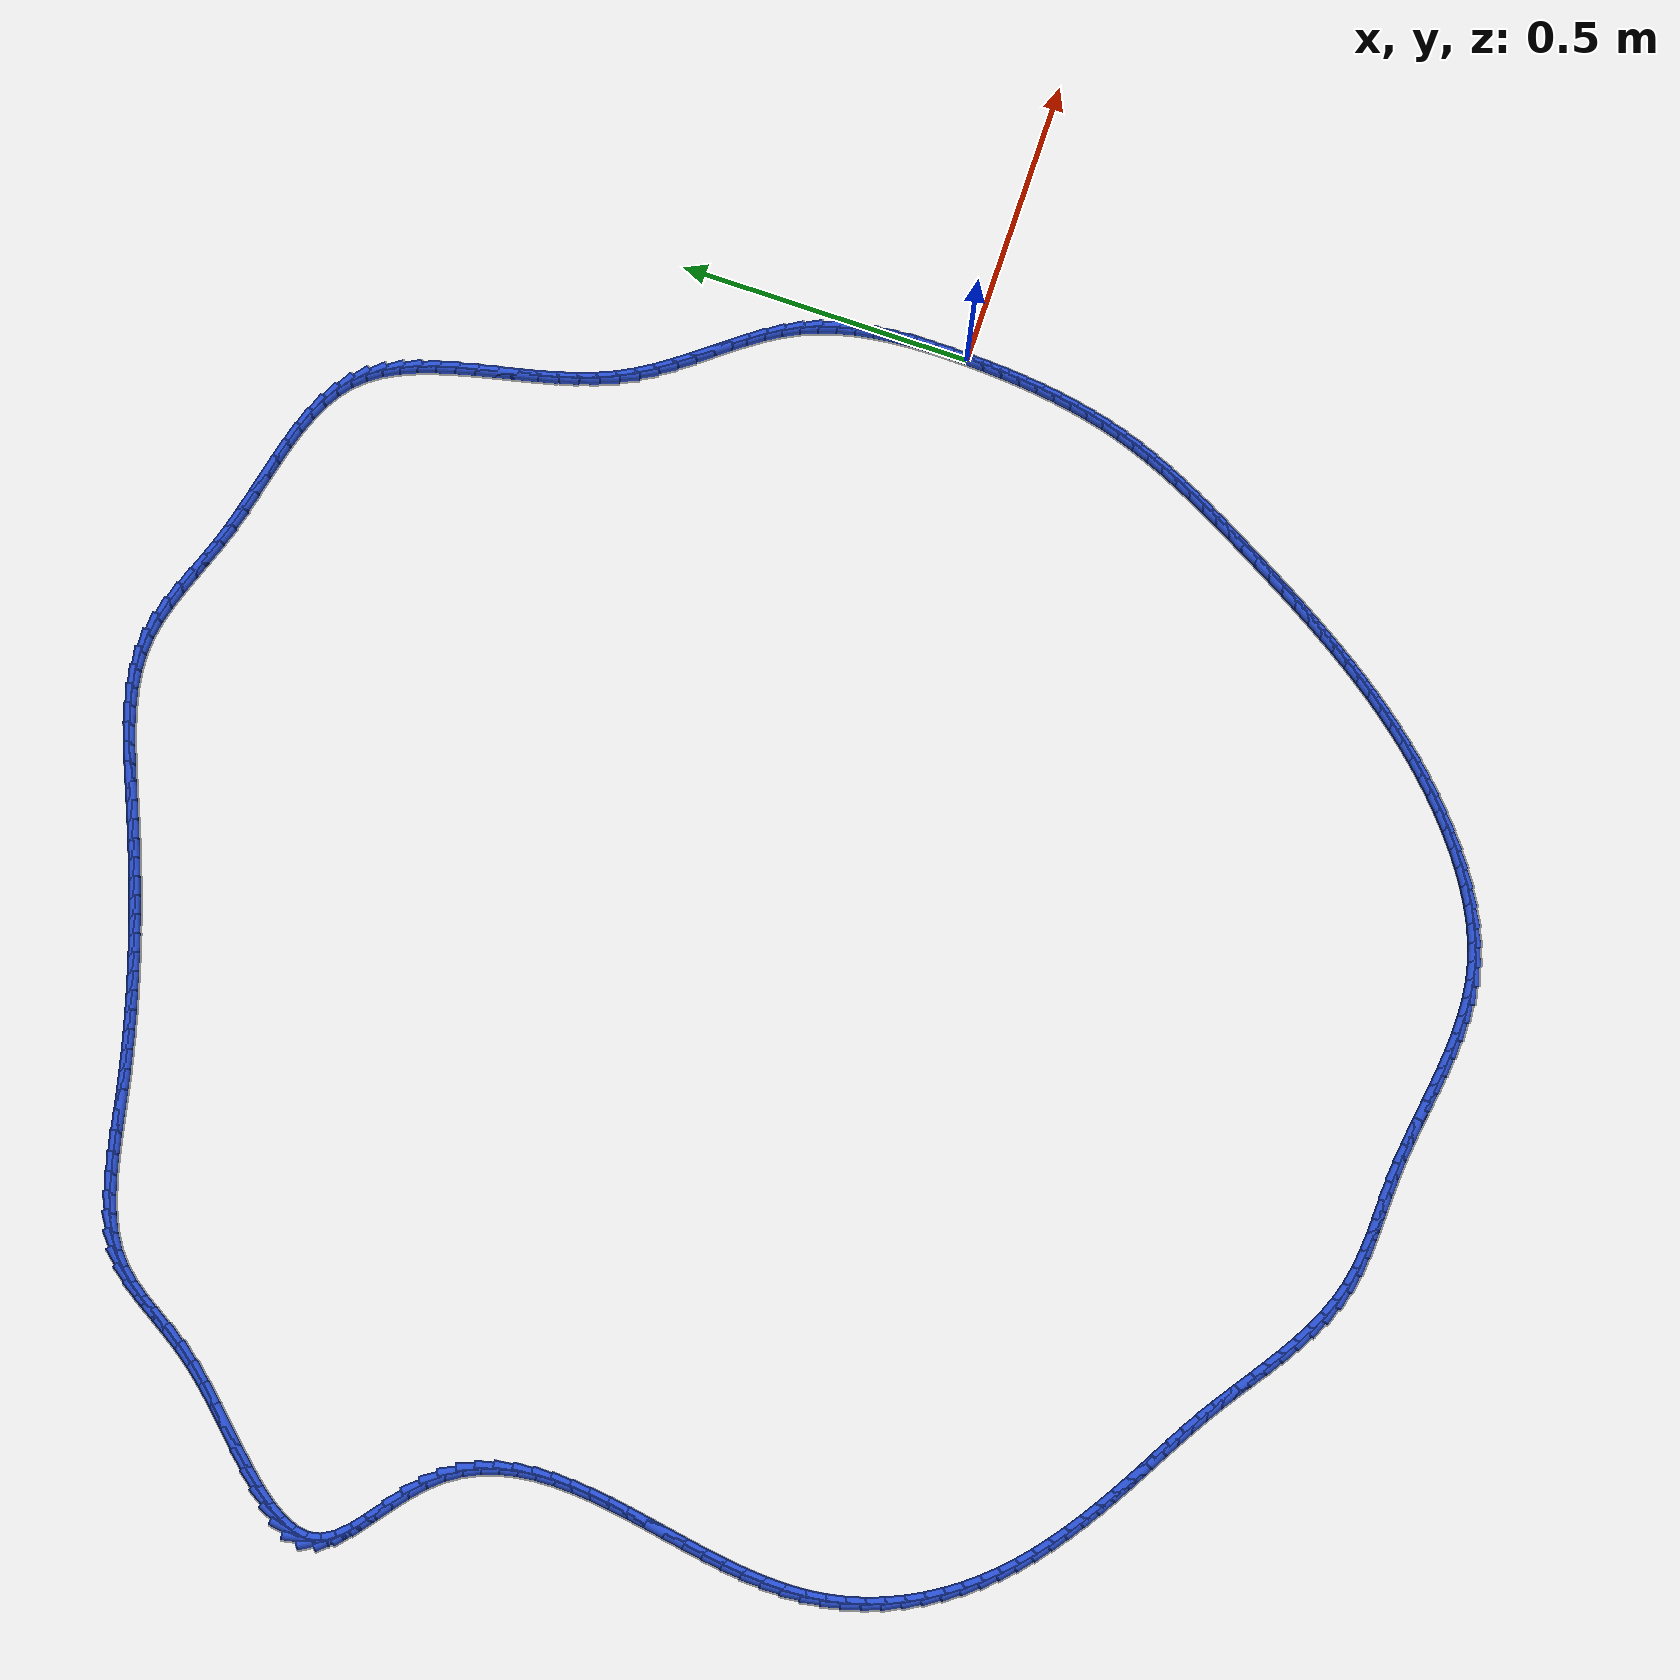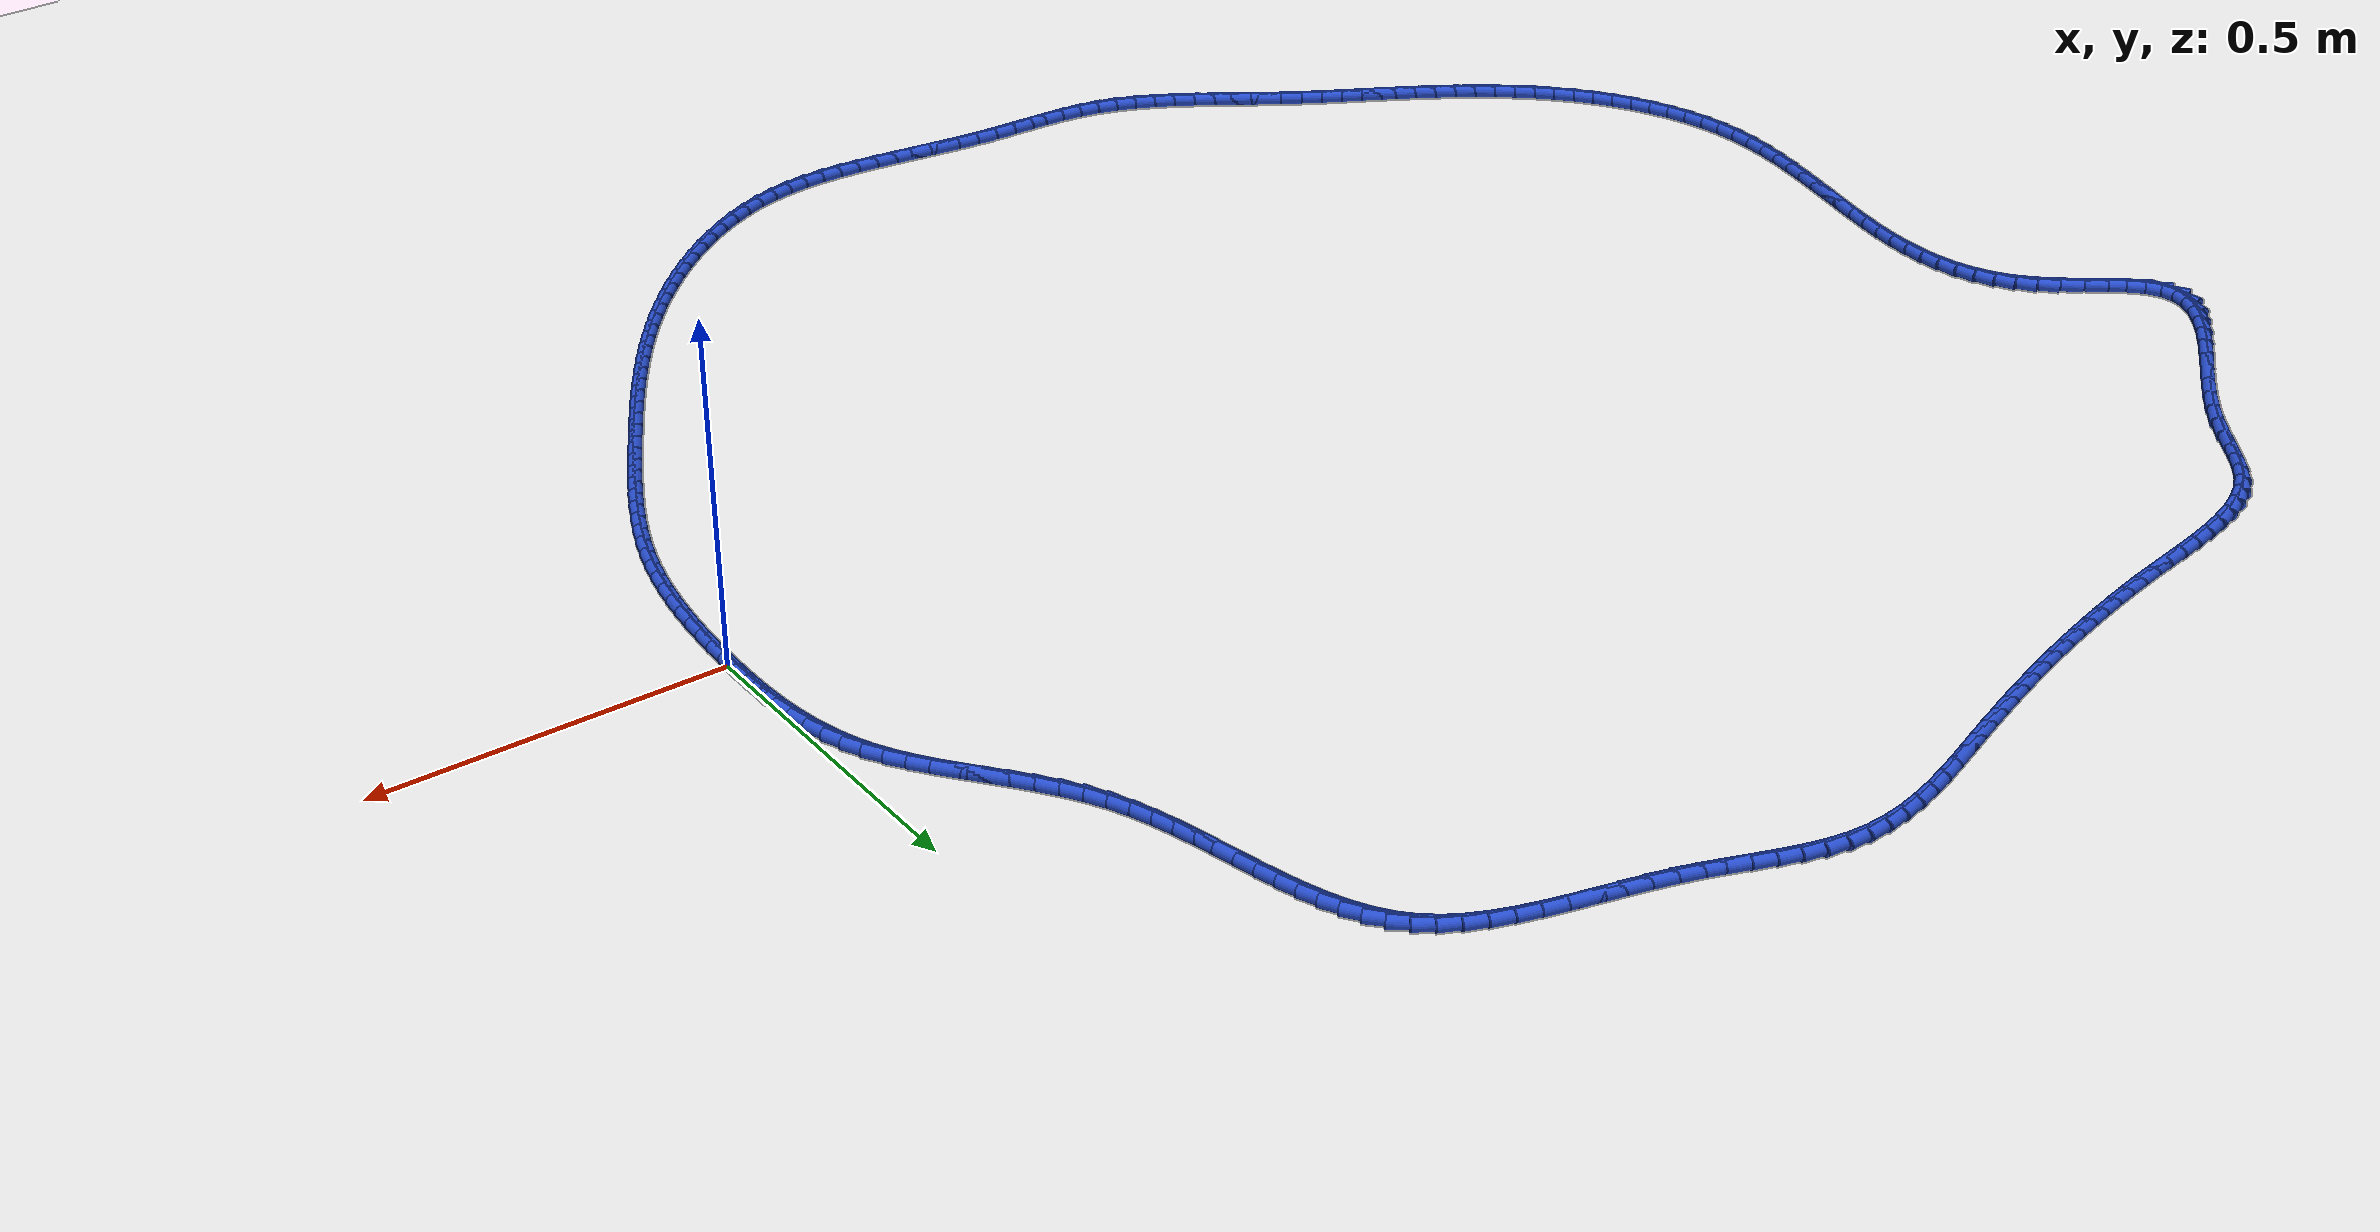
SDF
<sdf version="1.6">
 <world name="default">
  <light name="sun" type="directional">
   <pose>0 0 10 0 -0 0</pose>
   <diffuse>0.8 0.8 0.8 1</diffuse>
   <specular>0.2 0.2 0.2 1</specular>
   <attenuation>
    <range>1000</range>
    <constant>0.9</constant>
    <linear>0.01</linear>
    <quadratic>0.001</quadratic>
   </attenuation>
   <direction>-0.5 0.1 -0.9</direction>
  </light>
  <model name="ground_plane">
   <static>1</static>
   <link name="link">
    <collision name="collision">
     <geometry><plane><normal>0 0 1</normal><size>100 100</size></plane></geometry>
     <surface><friction><ode><mu>100</mu><mu2>50</mu2></ode></friction></surface>
    </collision>
    <visual name="visual">
     <cast_shadows>0</cast_shadows>
     <geometry><plane><normal>0 0 1</normal><size>100 100</size></plane></geometry>
     <material>
      <script><uri>file://media/materials/scripts/gazebo.material</uri><name>Gazebo/WhiteGlow</name></script>
     </material>
    </visual>
   </link>
  </model>
  <gravity>0 0 -9.8</gravity>
  <magnetic_field>6e-06 2.3e-05 -4.2e-05</magnetic_field>
  <atmosphere type="adiabatic"/>
  <physics name="default_physics" default="0" type="ode">
   <max_step_size>0.001</max_step_size>
   <real_time_factor>1</real_time_factor>
   <real_time_update_rate>1000</real_time_update_rate>
  </physics>
  <scene><ambient>0.4 0.4 0.4 1</ambient><background>0.7 0.7 0.7 1</background><shadows>1</shadows></scene>
  <spherical_coordinates>
   <surface_model>EARTH_WGS84</surface_model>
   <latitude_deg>0</latitude_deg>
   <longitude_deg>0</longitude_deg>
   <elevation>0</elevation>
   <heading_deg>0</heading_deg>
  </spherical_coordinates>
  <model name="line">
   <link name="link_0">
    <pose>-9.540979117872439e-18 -2.7755575615628914e-17 0.01 0 1.57 1.5509723002207512</pose>
    <collision name="collision">
     <geometry><cylinder><radius>0.01</radius><length>0.08</length></cylinder></geometry>
    </collision>
    <visual name="visual">
     <material>
      <script><name>Gazebo/Blue</name><uri>file://media/materials/scripts/gazebo.material</uri></script>
     </material>
     <geometry><cylinder><radius>0.01</radius><length>0.08</length></cylinder></geometry>
    </visual>
   </link>
   <link name="link_1">
    <pose>0.0006480934380880519 0.032688038170322134 0.01 0 1.57 -1.5671096846617614</pose>
    <collision name="collision">
     <geometry><cylinder><radius>0.01</radius><length>0.08</length></cylinder></geometry>
    </collision>
    <visual name="visual">
     <material>
      <script><name>Gazebo/Blue</name><uri>file://media/materials/scripts/gazebo.material</uri></script>
     </material>
     <geometry><cylinder><radius>0.01</radius><length>0.08</length></cylinder></geometry>
    </visual>
   </link>
   <link name="link_2">
    <pose>0.000527345814850162 0.06544062760986999 0.01 0 1.57 -1.5366535923674727</pose>
    <collision name="collision">
     <geometry><cylinder><radius>0.01</radius><length>0.08</length></cylinder></geometry>
    </collision>
    <visual name="visual">
     <material>
      <script><name>Gazebo/Blue</name><uri>file://media/materials/scripts/gazebo.material</uri></script>
     </material>
     <geometry><cylinder><radius>0.01</radius><length>0.08</length></cylinder></geometry>
    </visual>
   </link>
   <link name="link_3">
    <pose>-0.0005877928225679215 0.09808901699485471 0.01 0 1.57 -1.498795968035626</pose>
    <collision name="collision">
     <geometry><cylinder><radius>0.01</radius><length>0.08</length></cylinder></geometry>
    </collision>
    <visual name="visual">
     <material>
      <script><name>Gazebo/Blue</name><uri>file://media/materials/scripts/gazebo.material</uri></script>
     </material>
     <geometry><cylinder><radius>0.01</radius><length>0.08</length></cylinder></geometry>
    </visual>
   </link>
   <link name="link_4">
    <pose>-0.0029228724270204402 0.13046445500148754 0.01 0 1.57 -1.4529568356450675</pose>
    <collision name="collision">
     <geometry><cylinder><radius>0.01</radius><length>0.08</length></cylinder></geometry>
    </collision>
    <visual name="visual">
     <material>
      <script><name>Gazebo/Blue</name><uri>file://media/materials/scripts/gazebo.material</uri></script>
     </material>
     <geometry><cylinder><radius>0.01</radius><length>0.08</length></cylinder></geometry>
    </visual>
   </link>
   <link name="link_5">
    <pose>-0.00670344295136164 0.1623981903059797 0.01 0 1.57 -1.3984789537789857</pose>
    <collision name="collision">
     <geometry><cylinder><radius>0.01</radius><length>0.08</length></cylinder></geometry>
    </collision>
    <visual name="visual">
     <material>
      <script><name>Gazebo/Blue</name><uri>file://media/materials/scripts/gazebo.material</uri></script>
     </material>
     <geometry><cylinder><radius>0.01</radius><length>0.08</length></cylinder></geometry>
    </visual>
   </link>
   <link name="link_6">
    <pose>-0.012155054348445762 0.19372147158454245 0.01 0 1.57 -1.334705840565855</pose>
    <collision name="collision">
     <geometry><cylinder><radius>0.01</radius><length>0.08</length></cylinder></geometry>
    </collision>
    <visual name="visual">
     <material>
      <script><name>Gazebo/Blue</name><uri>file://media/materials/scripts/gazebo.material</uri></script>
     </material>
     <geometry><cylinder><radius>0.01</radius><length>0.08</length></cylinder></geometry>
    </visual>
   </link>
   <link name="link_7">
    <pose>-0.019503256571127038 0.2242655475133869 0.01 0 1.57 -1.2611061068454434</pose>
    <collision name="collision">
     <geometry><cylinder><radius>0.01</radius><length>0.08</length></cylinder></geometry>
    </collision>
    <visual name="visual">
     <material>
      <script><name>Gazebo/Blue</name><uri>file://media/materials/scripts/gazebo.material</uri></script>
     </material>
     <geometry><cylinder><radius>0.01</radius><length>0.08</length></cylinder></geometry>
    </visual>
   </link>
   <link name="link_8">
    <pose>-0.028973599572259735 0.2538616667687244 0.01 0 1.57 -1.1774538288376382</pose>
    <collision name="collision">
     <geometry><cylinder><radius>0.01</radius><length>0.08</length></cylinder></geometry>
    </collision>
    <visual name="visual">
     <material>
      <script><name>Gazebo/Blue</name><uri>file://media/materials/scripts/gazebo.material</uri></script>
     </material>
     <geometry><cylinder><radius>0.01</radius><length>0.08</length></cylinder></geometry>
    </visual>
   </link>
   <link name="link_9">
    <pose>-0.040791632058986144 0.28234107882616594 0.01 0 1.57 -1.0889719972497625</pose>
    <collision name="collision">
     <geometry><cylinder><radius>0.01</radius><length>0.08</length></cylinder></geometry>
    </collision>
    <visual name="visual">
     <material>
      <script><name>Gazebo/Blue</name><uri>file://media/materials/scripts/gazebo.material</uri></script>
     </material>
     <geometry><cylinder><radius>0.01</radius><length>0.08</length></cylinder></geometry>
    </visual>
   </link>
   <link name="link_10">
    <pose>-0.05505510315193037 0.3096170448844138 0.01 0 1.57 -1.0150823429295994</pose>
    <collision name="collision">
     <geometry><cylinder><radius>0.01</radius><length>0.08</length></cylinder></geometry>
    </collision>
    <visual name="visual">
     <material>
      <script><name>Gazebo/Blue</name><uri>file://media/materials/scripts/gazebo.material</uri></script>
     </material>
     <geometry><cylinder><radius>0.01</radius><length>0.08</length></cylinder></geometry>
    </visual>
   </link>
   <link name="link_11">
    <pose>-0.07138294812909438 0.33591009120728466 0.01 0 1.57 -0.9606677409715202</pose>
    <collision name="collision">
     <geometry><cylinder><radius>0.01</radius><length>0.08</length></cylinder></geometry>
    </collision>
    <visual name="visual">
     <material>
      <script><name>Gazebo/Blue</name><uri>file://media/materials/scripts/gazebo.material</uri></script>
     </material>
     <geometry><cylinder><radius>0.01</radius><length>0.08</length></cylinder></geometry>
    </visual>
   </link>
   <link name="link_12">
    <pose>-0.0892819881450799 0.3615126900851312 0.01 0 1.57 -0.9254292658346407</pose>
    <collision name="collision">
     <geometry><cylinder><radius>0.01</radius><length>0.08</length></cylinder></geometry>
    </collision>
    <visual name="visual">
     <material>
      <script><name>Gazebo/Blue</name><uri>file://media/materials/scripts/gazebo.material</uri></script>
     </material>
     <geometry><cylinder><radius>0.01</radius><length>0.08</length></cylinder></geometry>
    </visual>
   </link>
   <link name="link_13">
    <pose>-0.1082590443544886 0.38671731380830593 0.01 0 1.57 -0.9087521366788066</pose>
    <collision name="collision">
     <geometry><cylinder><radius>0.01</radius><length>0.08</length></cylinder></geometry>
    </collision>
    <visual name="visual">
     <material>
      <script><name>Gazebo/Blue</name><uri>file://media/materials/scripts/gazebo.material</uri></script>
     </material>
     <geometry><cylinder><radius>0.01</radius><length>0.08</length></cylinder></geometry>
    </visual>
   </link>
   <link name="link_14">
    <pose>-0.12782093791192217 0.41181643466716134 0.01 0 1.57 -0.9100836072281419</pose>
    <collision name="collision">
     <geometry><cylinder><radius>0.01</radius><length>0.08</length></cylinder></geometry>
    </collision>
    <visual name="visual">
     <material>
      <script><name>Gazebo/Blue</name><uri>file://media/materials/scripts/gazebo.material</uri></script>
     </material>
     <geometry><cylinder><radius>0.01</radius><length>0.08</length></cylinder></geometry>
    </visual>
   </link>
   <link name="link_15">
    <pose>-0.14747448997198237 0.4371025249520501 0.01 0 1.57 -0.9290889750747698</pose>
    <collision name="collision">
     <geometry><cylinder><radius>0.01</radius><length>0.08</length></cylinder></geometry>
    </collision>
    <visual name="visual">
     <material>
      <script><name>Gazebo/Blue</name><uri>file://media/materials/scripts/gazebo.material</uri></script>
     </material>
     <geometry><cylinder><radius>0.01</radius><length>0.08</length></cylinder></geometry>
    </visual>
   </link>
   <link name="link_16">
    <pose>-0.16672652168927088 0.4628680569533247 0.01 0 1.57 -0.9656273788621806</pose>
    <collision name="collision">
     <geometry><cylinder><radius>0.01</radius><length>0.08</length></cylinder></geometry>
    </collision>
    <visual name="visual">
     <material>
      <script><name>Gazebo/Blue</name><uri>file://media/materials/scripts/gazebo.material</uri></script>
     </material>
     <geometry><cylinder><radius>0.01</radius><length>0.08</length></cylinder></geometry>
    </visual>
   </link>
   <link name="link_17">
    <pose>-0.1850838542183893 0.48940550296133756 0.01 0 1.57 -1.0195694857574735</pose>
    <collision name="collision">
     <geometry><cylinder><radius>0.01</radius><length>0.08</length></cylinder></geometry>
    </collision>
    <visual name="visual">
     <material>
      <script><name>Gazebo/Blue</name><uri>file://media/materials/scripts/gazebo.material</uri></script>
     </material>
     <geometry><cylinder><radius>0.01</radius><length>0.08</length></cylinder></geometry>
    </visual>
   </link>
   <link name="link_18">
    <pose>-0.20205330871393937 0.5170073352664414 0.01 0 1.57 -1.0904457805162286</pose>
    <collision name="collision">
     <geometry><cylinder><radius>0.01</radius><length>0.08</length></cylinder></geometry>
    </collision>
    <visual name="visual">
     <material>
      <script><name>Gazebo/Blue</name><uri>file://media/materials/scripts/gazebo.material</uri></script>
     </material>
     <geometry><cylinder><radius>0.01</radius><length>0.08</length></cylinder></geometry>
    </visual>
   </link>
   <link name="link_19">
    <pose>-0.21714222876289765 0.5459656546807882 0.01 0 1.57 -1.1689932220289792</pose>
    <collision name="collision">
     <geometry><cylinder><radius>0.01</radius><length>0.08</length></cylinder></geometry>
    </collision>
    <visual name="visual">
     <material>
      <script><name>Gazebo/Blue</name><uri>file://media/materials/scripts/gazebo.material</uri></script>
     </material>
     <geometry><cylinder><radius>0.01</radius><length>0.08</length></cylinder></geometry>
    </visual>
   </link>
   <link name="link_20">
    <pose>-0.23008048812826426 0.5764143308016453 0.01 0 1.57 -1.2340977902375778</pose>
    <collision name="collision">
     <geometry><cylinder><radius>0.01</radius><length>0.08</length></cylinder></geometry>
    </collision>
    <visual name="visual">
     <material>
      <script><name>Gazebo/Blue</name><uri>file://media/materials/scripts/gazebo.material</uri></script>
     </material>
     <geometry><cylinder><radius>0.01</radius><length>0.08</length></cylinder></geometry>
    </visual>
   </link>
   <link name="link_21">
    <pose>-0.24116558325167514 0.6080836222300486 0.01 0 1.57 -1.283526651803879</pose>
    <collision name="collision">
     <geometry><cylinder><radius>0.01</radius><length>0.08</length></cylinder></geometry>
    </collision>
    <visual name="visual">
     <material>
      <script><name>Gazebo/Blue</name><uri>file://media/materials/scripts/gazebo.material</uri></script>
     </material>
     <geometry><cylinder><radius>0.01</radius><length>0.08</length></cylinder></geometry>
    </visual>
   </link>
   <link name="link_22">
    <pose>-0.25078420423326886 0.6406403659619423 0.01 0 1.57 -1.3184104169941269</pose>
    <collision name="collision">
     <geometry><cylinder><radius>0.01</radius><length>0.08</length></cylinder></geometry>
    </collision>
    <visual name="visual">
     <material>
      <script><name>Gazebo/Blue</name><uri>file://media/materials/scripts/gazebo.material</uri></script>
     </material>
     <geometry><cylinder><radius>0.01</radius><length>0.08</length></cylinder></geometry>
    </visual>
   </link>
   <link name="link_23">
    <pose>-0.259323041173184 0.6737513989932696 0.01 0 1.57 -1.3396237344587576</pose>
    <collision name="collision">
     <geometry><cylinder><radius>0.01</radius><length>0.08</length></cylinder></geometry>
    </collision>
    <visual name="visual">
     <material>
      <script><name>Gazebo/Blue</name><uri>file://media/materials/scripts/gazebo.material</uri></script>
     </material>
     <geometry><cylinder><radius>0.01</radius><length>0.08</length></cylinder></geometry>
    </visual>
   </link>
   <link name="link_24">
    <pose>-0.2671687841715592 0.7070835583199749 0.01 0 1.57 -1.3476256977767074</pose>
    <collision name="collision">
     <geometry><cylinder><radius>0.01</radius><length>0.08</length></cylinder></geometry>
    </collision>
    <visual name="visual">
     <material>
      <script><name>Gazebo/Blue</name><uri>file://media/materials/scripts/gazebo.material</uri></script>
     </material>
     <geometry><cylinder><radius>0.01</radius><length>0.08</length></cylinder></geometry>
    </visual>
   </link>
   <link name="link_25">
    <pose>-0.27470812332853284 0.7403036809380015 0.01 0 1.57 -1.3423705962240982</pose>
    <collision name="collision">
     <geometry><cylinder><radius>0.01</radius><length>0.08</length></cylinder></geometry>
    </collision>
    <visual name="visual">
     <material>
      <script><name>Gazebo/Blue</name><uri>file://media/materials/scripts/gazebo.material</uri></script>
     </material>
     <geometry><cylinder><radius>0.01</radius><length>0.08</length></cylinder></geometry>
    </visual>
   </link>
   <link name="link_26">
    <pose>-0.28232774874424355 0.773078603843293 0.01 0 1.57 -1.3232466426435803</pose>
    <collision name="collision">
     <geometry><cylinder><radius>0.01</radius><length>0.08</length></cylinder></geometry>
    </collision>
    <visual name="visual">
     <material>
      <script><name>Gazebo/Blue</name><uri>file://media/materials/scripts/gazebo.material</uri></script>
     </material>
     <geometry><cylinder><radius>0.01</radius><length>0.08</length></cylinder></geometry>
    </visual>
   </link>
   <link name="link_27">
    <pose>-0.29041435051883 0.8050751640317938 0.01 0 1.57 -1.2890285368582663</pose>
    <collision name="collision">
     <geometry><cylinder><radius>0.01</radius><length>0.08</length></cylinder></geometry>
    </collision>
    <visual name="visual">
     <material>
      <script><name>Gazebo/Blue</name><uri>file://media/materials/scripts/gazebo.material</uri></script>
     </material>
     <geometry><cylinder><radius>0.01</radius><length>0.08</length></cylinder></geometry>
    </visual>
   </link>
   <link name="link_28">
    <pose>-0.29935461875243063 0.8359601984994469 0.01 0 1.57 -1.2378633953827356</pose>
    <collision name="collision">
     <geometry><cylinder><radius>0.01</radius><length>0.08</length></cylinder></geometry>
    </collision>
    <visual name="visual">
     <material>
      <script><name>Gazebo/Blue</name><uri>file://media/materials/scripts/gazebo.material</uri></script>
     </material>
     <geometry><cylinder><radius>0.01</radius><length>0.08</length></cylinder></geometry>
    </visual>
   </link>
   <link name="link_29">
    <pose>-0.309535243545184 0.8654005442421968 0.01 0 1.57 -1.1673617174606643</pose>
    <collision name="collision">
     <geometry><cylinder><radius>0.01</radius><length>0.08</length></cylinder></geometry>
    </collision>
    <visual name="visual">
     <material>
      <script><name>Gazebo/Blue</name><uri>file://media/materials/scripts/gazebo.material</uri></script>
     </material>
     <geometry><cylinder><radius>0.01</radius><length>0.08</length></cylinder></geometry>
    </visual>
   </link>
   <link name="link_30">
    <pose>-0.321342914997229 0.8930630382559871 0.01 0 1.57 -1.0749479529999244</pose>
    <collision name="collision">
     <geometry><cylinder><radius>0.01</radius><length>0.08</length></cylinder></geometry>
    </collision>
    <visual name="visual">
     <material>
      <script><name>Gazebo/Blue</name><uri>file://media/materials/scripts/gazebo.material</uri></script>
     </material>
     <geometry><cylinder><radius>0.01</radius><length>0.08</length></cylinder></geometry>
    </visual>
   </link>
   <link name="link_31">
    <pose>-0.3351643232087037 0.9186145175367612 0.01 0 1.57 -0.9587145743723529</pose>
    <collision name="collision">
     <geometry><cylinder><radius>0.01</radius><length>0.08</length></cylinder></geometry>
    </collision>
    <visual name="visual">
     <material>
      <script><name>Gazebo/Blue</name><uri>file://media/materials/scripts/gazebo.material</uri></script>
     </material>
     <geometry><cylinder><radius>0.01</radius><length>0.08</length></cylinder></geometry>
    </visual>
   </link>
   <link name="link_32">
    <pose>-0.35138615827974695 0.9417218190804629 0.01 0 1.57 -0.8189661553435489</pose>
    <collision name="collision">
     <geometry><cylinder><radius>0.01</radius><length>0.08</length></cylinder></geometry>
    </collision>
    <visual name="visual">
     <material>
      <script><name>Gazebo/Blue</name><uri>file://media/materials/scripts/gazebo.material</uri></script>
     </material>
     <geometry><cylinder><radius>0.01</radius><length>0.08</length></cylinder></geometry>
    </visual>
   </link>
   <link name="link_33">
    <pose>-0.37039510236368356 0.9620517876873002 0.01 0 1.57 -0.6672578157226929</pose>
    <collision name="collision">
     <geometry><cylinder><radius>0.01</radius><length>0.08</length></cylinder></geometry>
    </collision>
    <visual name="visual">
     <material>
      <script><name>Gazebo/Blue</name><uri>file://media/materials/scripts/gazebo.material</uri></script>
     </material>
     <geometry><cylinder><radius>0.01</radius><length>0.08</length></cylinder></geometry>
    </visual>
   </link>
   <link name="link_34">
    <pose>-0.3924331433485759 0.9794133668935624 0.01 0 1.57 -0.5353669460939533</pose>
    <collision name="collision">
     <geometry><cylinder><radius>0.01</radius><length>0.08</length></cylinder></geometry>
    </collision>
    <visual name="visual">
     <material>
      <script><name>Gazebo/Blue</name><uri>file://media/materials/scripts/gazebo.material</uri></script>
     </material>
     <geometry><cylinder><radius>0.01</radius><length>0.08</length></cylinder></geometry>
    </visual>
   </link>
   <link name="link_35">
    <pose>-0.41722808075413903 0.9941204650806784 0.01 0 1.57 -0.4306078056824694</pose>
    <collision name="collision">
     <geometry><cylinder><radius>0.01</radius><length>0.08</length></cylinder></geometry>
    </collision>
    <visual name="visual">
     <material>
      <script><name>Gazebo/Blue</name><uri>file://media/materials/scripts/gazebo.material</uri></script>
     </material>
     <geometry><cylinder><radius>0.01</radius><length>0.08</length></cylinder></geometry>
    </visual>
   </link>
   <link name="link_36">
    <pose>-0.4443935476967348 1.0065991091137647 0.01 0 1.57 -0.35108244564889207</pose>
    <collision name="collision">
     <geometry><cylinder><radius>0.01</radius><length>0.08</length></cylinder></geometry>
    </collision>
    <visual name="visual">
     <material>
      <script><name>Gazebo/Blue</name><uri>file://media/materials/scripts/gazebo.material</uri></script>
     </material>
     <geometry><cylinder><radius>0.01</radius><length>0.08</length></cylinder></geometry>
    </visual>
   </link>
   <link name="link_37">
    <pose>-0.47354317729272516 1.0172753258579377 0.01 0 1.57 -0.293710655829187</pose>
    <collision name="collision">
     <geometry><cylinder><radius>0.01</radius><length>0.08</length></cylinder></geometry>
    </collision>
    <visual name="visual">
     <material>
      <script><name>Gazebo/Blue</name><uri>file://media/materials/scripts/gazebo.material</uri></script>
     </material>
     <geometry><cylinder><radius>0.01</radius><length>0.08</length></cylinder></geometry>
    </visual>
   </link>
   <link name="link_38">
    <pose>-0.504290602658472 1.026575142178314 0.01 0 1.57 -0.2555441786680853</pose>
    <collision name="collision">
     <geometry><cylinder><radius>0.01</radius><length>0.08</length></cylinder></geometry>
    </collision>
    <visual name="visual">
     <material>
      <script><name>Gazebo/Blue</name><uri>file://media/materials/scripts/gazebo.material</uri></script>
     </material>
     <geometry><cylinder><radius>0.01</radius><length>0.08</length></cylinder></geometry>
    </visual>
   </link>
   <link name="link_39">
    <pose>-0.5362494569103372 1.0349245849400102 0.01 0 1.57 -0.23430316299109025</pose>
    <collision name="collision">
     <geometry><cylinder><radius>0.01</radius><length>0.08</length></cylinder></geometry>
    </collision>
    <visual name="visual">
     <material>
      <script><name>Gazebo/Blue</name><uri>file://media/materials/scripts/gazebo.material</uri></script>
     </material>
     <geometry><cylinder><radius>0.01</radius><length>0.08</length></cylinder></geometry>
    </visual>
   </link>
   <link name="link_40">
    <pose>-0.569033373164683 1.0427496810081427 0.01 0 1.57 -0.22851341701971878</pose>
    <collision name="collision">
     <geometry><cylinder><radius>0.01</radius><length>0.08</length></cylinder></geometry>
    </collision>
    <visual name="visual">
     <material>
      <script><name>Gazebo/Blue</name><uri>file://media/materials/scripts/gazebo.material</uri></script>
     </material>
     <geometry><cylinder><radius>0.01</radius><length>0.08</length></cylinder></geometry>
    </visual>
   </link>
   <link name="link_41">
    <pose>-0.6022559845378709 1.0504764572478278 0.01 0 1.57 -0.23749049462618627</pose>
    <collision name="collision">
     <geometry><cylinder><radius>0.01</radius><length>0.08</length></cylinder></geometry>
    </collision>
    <visual name="visual">
     <material>
      <script><name>Gazebo/Blue</name><uri>file://media/materials/scripts/gazebo.material</uri></script>
     </material>
     <geometry><cylinder><radius>0.01</radius><length>0.08</length></cylinder></geometry>
    </visual>
   </link>
   <link name="link_42">
    <pose>-0.6355309241462634 1.0585309405241823 0.01 0 1.57 -0.2612818216790445</pose>
    <collision name="collision">
     <geometry><cylinder><radius>0.01</radius><length>0.08</length></cylinder></geometry>
    </collision>
    <visual name="visual">
     <material>
      <script><name>Gazebo/Blue</name><uri>file://media/materials/scripts/gazebo.material</uri></script>
     </material>
     <geometry><cylinder><radius>0.01</radius><length>0.08</length></cylinder></geometry>
    </visual>
   </link>
   <link name="link_43">
    <pose>-0.6684718251062219 1.0673391577023223 0.01 0 1.57 -0.29998683237778345</pose>
    <collision name="collision">
     <geometry><cylinder><radius>0.01</radius><length>0.08</length></cylinder></geometry>
    </collision>
    <visual name="visual">
     <material>
      <script><name>Gazebo/Blue</name><uri>file://media/materials/scripts/gazebo.material</uri></script>
     </material>
     <geometry><cylinder><radius>0.01</radius><length>0.08</length></cylinder></geometry>
    </visual>
   </link>
   <link name="link_44">
    <pose>-0.7007013021845167 1.0773084382759213 0.01 0 1.57 -0.3371212285265319</pose>
    <collision name="collision">
     <geometry><cylinder><radius>0.01</radius><length>0.08</length></cylinder></geometry>
    </collision>
    <visual name="visual">
     <material>
      <script><name>Gazebo/Blue</name><uri>file://media/materials/scripts/gazebo.material</uri></script>
     </material>
     <geometry><cylinder><radius>0.01</radius><length>0.08</length></cylinder></geometry>
    </visual>
   </link>
   <link name="link_45">
    <pose>-0.7320980448267572 1.0883130333877695 0.01 0 1.57 -0.3528521597925134</pose>
    <collision name="collision">
     <geometry><cylinder><radius>0.01</radius><length>0.08</length></cylinder></geometry>
    </collision>
    <visual name="visual">
     <material>
      <script><name>Gazebo/Blue</name><uri>file://media/materials/scripts/gazebo.material</uri></script>
     </material>
     <geometry><cylinder><radius>0.01</radius><length>0.08</length></cylinder></geometry>
    </visual>
   </link>
   <link name="link_46">
    <pose>-0.7628277672682247 1.0996296860543815 0.01 0 1.57 -0.3451491324614072</pose>
    <collision name="collision">
     <geometry><cylinder><radius>0.01</radius><length>0.08</length></cylinder></geometry>
    </collision>
    <visual name="visual">
     <material>
      <script><name>Gazebo/Blue</name><uri>file://media/materials/scripts/gazebo.material</uri></script>
     </material>
     <geometry><cylinder><radius>0.01</radius><length>0.08</length></cylinder></geometry>
    </visual>
   </link>
   <link name="link_47">
    <pose>-0.7930713806897643 1.110503503354208 0.01 0 1.57 -0.3126027913945446</pose>
    <collision name="collision">
     <geometry><cylinder><radius>0.01</radius><length>0.08</length></cylinder></geometry>
    </collision>
    <visual name="visual">
     <material>
      <script><name>Gazebo/Blue</name><uri>file://media/materials/scripts/gazebo.material</uri></script>
     </material>
     <geometry><cylinder><radius>0.01</radius><length>0.08</length></cylinder></geometry>
    </visual>
   </link>
   <link name="link_48">
    <pose>-0.8230097962722206 1.1201795923657007 0.01 0 1.57 -0.2534817061256791</pose>
    <collision name="collision">
     <geometry><cylinder><radius>0.01</radius><length>0.08</length></cylinder></geometry>
    </collision>
    <visual name="visual">
     <material>
      <script><name>Gazebo/Blue</name><uri>file://media/materials/scripts/gazebo.material</uri></script>
     </material>
     <geometry><cylinder><radius>0.01</radius><length>0.08</length></cylinder></geometry>
    </visual>
   </link>
   <link name="link_49">
    <pose>-0.8528239251964391 1.1279030601673097 0.01 0 1.57 -0.16636973626836798</pose>
    <collision name="collision">
     <geometry><cylinder><radius>0.01</radius><length>0.08</length></cylinder></geometry>
    </collision>
    <visual name="visual">
     <material>
      <script><name>Gazebo/Blue</name><uri>file://media/materials/scripts/gazebo.material</uri></script>
     </material>
     <geometry><cylinder><radius>0.01</radius><length>0.08</length></cylinder></geometry>
    </visual>
   </link>
   <link name="link_50">
    <pose>-0.8826946786432639 1.1329190138374858 0.01 0 1.57 -0.0527953939663738</pose>
    <collision name="collision">
     <geometry><cylinder><radius>0.01</radius><length>0.08</length></cylinder></geometry>
    </collision>
    <visual name="visual">
     <material>
      <script><name>Gazebo/Blue</name><uri>file://media/materials/scripts/gazebo.material</uri></script>
     </material>
     <geometry><cylinder><radius>0.01</radius><length>0.08</length></cylinder></geometry>
    </visual>
   </link>
   <link name="link_51">
    <pose>-0.9127953869333578 1.1345096707728224 0.01 0 1.57 0.06277970974127081</pose>
    <collision name="collision">
     <geometry><cylinder><radius>0.01</radius><length>0.08</length></cylinder></geometry>
    </collision>
    <visual name="visual">
     <material>
      <script><name>Gazebo/Blue</name><uri>file://media/materials/scripts/gazebo.material</uri></script>
     </material>
     <geometry><cylinder><radius>0.01</radius><length>0.08</length></cylinder></geometry>
    </visual>
   </link>
   <link name="link_52">
    <pose>-0.9431680025323153 1.1326003777617155 0.01 0 1.57 0.16017281049282436</pose>
    <collision name="collision">
     <geometry><cylinder><radius>0.01</radius><length>0.08</length></cylinder></geometry>
    </collision>
    <visual name="visual">
     <material>
      <script><name>Gazebo/Blue</name><uri>file://media/materials/scripts/gazebo.material</uri></script>
     </material>
     <geometry><cylinder><radius>0.01</radius><length>0.08</length></cylinder></geometry>
    </visual>
   </link>
   <link name="link_53">
    <pose>-0.9737432990763977 1.1276607314043199 0.01 0 1.57 0.23905199526261023</pose>
    <collision name="collision">
     <geometry><cylinder><radius>0.01</radius><length>0.08</length></cylinder></geometry>
    </collision>
    <visual name="visual">
     <material>
      <script><name>Gazebo/Blue</name><uri>file://media/materials/scripts/gazebo.material</uri></script>
     </material>
     <geometry><cylinder><radius>0.01</radius><length>0.08</length></cylinder></geometry>
    </visual>
   </link>
   <link name="link_54">
    <pose>-1.0044485444715323 1.1201774897791539 0.01 0 1.57 0.3007158586468575</pose>
    <collision name="collision">
     <geometry><cylinder><radius>0.01</radius><length>0.08</length></cylinder></geometry>
    </collision>
    <visual name="visual">
     <material>
      <script><name>Gazebo/Blue</name><uri>file://media/materials/scripts/gazebo.material</uri></script>
     </material>
     <geometry><cylinder><radius>0.01</radius><length>0.08</length></cylinder></geometry>
    </visual>
   </link>
   <link name="link_55">
    <pose>-1.035211006623647 1.110637410964738 0.01 0 1.57 0.34674294993567206</pose>
    <collision name="collision">
     <geometry><cylinder><radius>0.01</radius><length>0.08</length></cylinder></geometry>
    </collision>
    <visual name="visual">
     <material>
      <script><name>Gazebo/Blue</name><uri>file://media/materials/scripts/gazebo.material</uri></script>
     </material>
     <geometry><cylinder><radius>0.01</radius><length>0.08</length></cylinder></geometry>
    </visual>
   </link>
   <link name="link_56">
    <pose>-1.065957953438669 1.0995272530395916 0.01 0 1.57 0.3785365288893354</pose>
    <collision name="collision">
     <geometry><cylinder><radius>0.01</radius><length>0.08</length></cylinder></geometry>
    </collision>
    <visual name="visual">
     <material>
      <script><name>Gazebo/Blue</name><uri>file://media/materials/scripts/gazebo.material</uri></script>
     </material>
     <geometry><cylinder><radius>0.01</radius><length>0.08</length></cylinder></geometry>
    </visual>
   </link>
   <link name="link_57">
    <pose>-1.0966166528225265 1.0873337740822344 0.01 0 1.57 0.397098282216129</pose>
    <collision name="collision">
     <geometry><cylinder><radius>0.01</radius><length>0.08</length></cylinder></geometry>
    </collision>
    <visual name="visual">
     <material>
      <script><name>Gazebo/Blue</name><uri>file://media/materials/scripts/gazebo.material</uri></script>
     </material>
     <geometry><cylinder><radius>0.01</radius><length>0.08</length></cylinder></geometry>
    </visual>
   </link>
   <link name="link_58">
    <pose>-1.1271143726811463 1.0745437321711864 0.01 0 1.57 0.4029237108310625</pose>
    <collision name="collision">
     <geometry><cylinder><radius>0.01</radius><length>0.08</length></cylinder></geometry>
    </collision>
    <visual name="visual">
     <material>
      <script><name>Gazebo/Blue</name><uri>file://media/materials/scripts/gazebo.material</uri></script>
     </material>
     <geometry><cylinder><radius>0.01</radius><length>0.08</length></cylinder></geometry>
    </visual>
   </link>
   <link name="link_59">
    <pose>-1.1573783809204568 1.061643885384967 0.01 0 1.57 0.39751565663080074</pose>
    <collision name="collision">
     <geometry><cylinder><radius>0.01</radius><length>0.08</length></cylinder></geometry>
    </collision>
    <visual name="visual">
     <material>
      <script><name>Gazebo/Blue</name><uri>file://media/materials/scripts/gazebo.material</uri></script>
     </material>
     <geometry><cylinder><radius>0.01</radius><length>0.08</length></cylinder></geometry>
    </visual>
   </link>
   <link name="link_60">
    <pose>-1.187353237792166 1.0490584065122837 0.01 0 1.57 0.38870804504021667</pose>
    <collision name="collision">
     <geometry><cylinder><radius>0.01</radius><length>0.08</length></cylinder></geometry>
    </collision>
    <visual name="visual">
     <material>
      <script><name>Gazebo/Blue</name><uri>file://media/materials/scripts/gazebo.material</uri></script>
     </material>
     <geometry><cylinder><radius>0.01</radius><length>0.08</length></cylinder></geometry>
    </visual>
   </link>
   <link name="link_61">
    <pose>-1.2170732323509796 1.0368867175410643 0.01 0 1.57 0.37910753694340543</pose>
    <collision name="collision">
     <geometry><cylinder><radius>0.01</radius><length>0.08</length></cylinder></geometry>
    </collision>
    <visual name="visual">
     <material>
      <script><name>Gazebo/Blue</name><uri>file://media/materials/scripts/gazebo.material</uri></script>
     </material>
     <geometry><cylinder><radius>0.01</radius><length>0.08</length></cylinder></geometry>
    </visual>
   </link>
   <link name="link_62">
    <pose>-1.2466016678025291 1.0251232310482887 0.01 0 1.57 0.36874794204758904</pose>
    <collision name="collision">
     <geometry><cylinder><radius>0.01</radius><length>0.08</length></cylinder></geometry>
    </collision>
    <visual name="visual">
     <material>
      <script><name>Gazebo/Blue</name><uri>file://media/materials/scripts/gazebo.material</uri></script>
     </material>
     <geometry><cylinder><radius>0.01</radius><length>0.08</length></cylinder></geometry>
    </visual>
   </link>
   <link name="link_63">
    <pose>-1.27600186196344 1.0137623067301282 0.01 0 1.57 0.35767268551169923</pose>
    <collision name="collision">
     <geometry><cylinder><radius>0.01</radius><length>0.08</length></cylinder></geometry>
    </collision>
    <visual name="visual">
     <material>
      <script><name>Gazebo/Blue</name><uri>file://media/materials/scripts/gazebo.material</uri></script>
     </material>
     <geometry><cylinder><radius>0.01</radius><length>0.08</length></cylinder></geometry>
    </visual>
   </link>
   <link name="link_64">
    <pose>-1.3053371326503358 1.0027983042827555 0.01 0 1.57 0.34593583188813853</pose>
    <collision name="collision">
     <geometry><cylinder><radius>0.01</radius><length>0.08</length></cylinder></geometry>
    </collision>
    <visual name="visual">
     <material>
      <script><name>Gazebo/Blue</name><uri>file://media/materials/scripts/gazebo.material</uri></script>
     </material>
     <geometry><cylinder><radius>0.01</radius><length>0.08</length></cylinder></geometry>
    </visual>
   </link>
   <link name="link_65">
    <pose>-1.3346707976798418 0.9922255834023425 0.01 0 1.57 0.3336014136862844</pose>
    <collision name="collision">
     <geometry><cylinder><radius>0.01</radius><length>0.08</length></cylinder></geometry>
    </collision>
    <visual name="visual">
     <material>
      <script><name>Gazebo/Blue</name><uri>file://media/materials/scripts/gazebo.material</uri></script>
     </material>
     <geometry><cylinder><radius>0.01</radius><length>0.08</length></cylinder></geometry>
    </visual>
   </link>
   <link name="link_66">
    <pose>-1.3640661748685832 0.9820385037850615 0.01 0 1.57 0.3207423926522801</pose>
    <collision name="collision">
     <geometry><cylinder><radius>0.01</radius><length>0.08</length></cylinder></geometry>
    </collision>
    <visual name="visual">
     <material>
      <script><name>Gazebo/Blue</name><uri>file://media/materials/scripts/gazebo.material</uri></script>
     </material>
     <geometry><cylinder><radius>0.01</radius><length>0.08</length></cylinder></geometry>
    </visual>
   </link>
   <link name="link_67">
    <pose>-1.393586582033184 0.9722314251270845 0.01 0 1.57 0.30743928002870974</pose>
    <collision name="collision">
     <geometry><cylinder><radius>0.01</radius><length>0.08</length></cylinder></geometry>
    </collision>
    <visual name="visual">
     <material>
      <script><name>Gazebo/Blue</name><uri>file://media/materials/scripts/gazebo.material</uri></script>
     </material>
     <geometry><cylinder><radius>0.01</radius><length>0.08</length></cylinder></geometry>
    </visual>
   </link>
   <link name="link_68">
    <pose>-1.4232953369902692 0.9627987071245837 0.01 0 1.57 0.29377846605774915</pose>
    <collision name="collision">
     <geometry><cylinder><radius>0.01</radius><length>0.08</length></cylinder></geometry>
    </collision>
    <visual name="visual">
     <material>
      <script><name>Gazebo/Blue</name><uri>file://media/materials/scripts/gazebo.material</uri></script>
     </material>
     <geometry><cylinder><radius>0.01</radius><length>0.08</length></cylinder></geometry>
    </visual>
   </link>
   <link name="link_69">
    <pose>-1.4532557575564637 0.9537347094737318 0.01 0 1.57 0.27985033041606083</pose>
    <collision name="collision">
     <geometry><cylinder><radius>0.01</radius><length>0.08</length></cylinder></geometry>
    </collision>
    <visual name="visual">
     <material>
      <script><name>Gazebo/Blue</name><uri>file://media/materials/scripts/gazebo.material</uri></script>
     </material>
     <geometry><cylinder><radius>0.01</radius><length>0.08</length></cylinder></geometry>
    </visual>
   </link>
   <link name="link_70">
    <pose>-1.483531161548392 0.9450337918707004 0.01 0 1.57 0.26574722159702757</pose>
    <collision name="collision">
     <geometry><cylinder><radius>0.01</radius><length>0.08</length></cylinder></geometry>
    </collision>
    <visual name="visual">
     <material>
      <script><name>Gazebo/Blue</name><uri>file://media/materials/scripts/gazebo.material</uri></script>
     </material>
     <geometry><cylinder><radius>0.01</radius><length>0.08</length></cylinder></geometry>
    </visual>
   </link>
   <link name="link_71">
    <pose>-1.514184866782678 0.9366903140116618 0.01 0 1.57 0.2515614024798977</pose>
    <collision name="collision">
     <geometry><cylinder><radius>0.01</radius><length>0.08</length></cylinder></geometry>
    </collision>
    <visual name="visual">
     <material>
      <script><name>Gazebo/Blue</name><uri>file://media/materials/scripts/gazebo.material</uri></script>
     </material>
     <geometry><cylinder><radius>0.01</radius><length>0.08</length></cylinder></geometry>
    </visual>
   </link>
   <link name="link_72">
    <pose>-1.5452801910759477 0.9286986355927882 0.01 0 1.57 0.23738306031666873</pose>
    <collision name="collision">
     <geometry><cylinder><radius>0.01</radius><length>0.08</length></cylinder></geometry>
    </collision>
    <visual name="visual">
     <material>
      <script><name>Gazebo/Blue</name><uri>file://media/materials/scripts/gazebo.material</uri></script>
     </material>
     <geometry><cylinder><radius>0.01</radius><length>0.08</length></cylinder></geometry>
    </visual>
   </link>
   <link name="link_73">
    <pose>-1.5768804522448245 0.9210531163102518 0.01 0 1.57 0.22329847208813447</pose>
    <collision name="collision">
     <geometry><cylinder><radius>0.01</radius><length>0.08</length></cylinder></geometry>
    </collision>
    <visual name="visual">
     <material>
      <script><name>Gazebo/Blue</name><uri>file://media/materials/scripts/gazebo.material</uri></script>
     </material>
     <geometry><cylinder><radius>0.01</radius><length>0.08</length></cylinder></geometry>
    </visual>
   </link>
   <link name="link_74">
    <pose>-1.6090489681059348 0.9137481158602249 0.01 0 1.57 0.21053870921814336</pose>
    <collision name="collision">
     <geometry><cylinder><radius>0.01</radius><length>0.08</length></cylinder></geometry>
    </collision>
    <visual name="visual">
     <material>
      <script><name>Gazebo/Blue</name><uri>file://media/materials/scripts/gazebo.material</uri></script>
     </material>
     <geometry><cylinder><radius>0.01</radius><length>0.08</length></cylinder></geometry>
    </visual>
   </link>
   <link name="link_75">
    <pose>-1.641809948272826 0.9067469079319925 0.01 0 1.57 0.20856906568955896</pose>
    <collision name="collision">
     <geometry><cylinder><radius>0.01</radius><length>0.08</length></cylinder></geometry>
    </collision>
    <visual name="visual">
     <material>
      <script><name>Gazebo/Blue</name><uri>file://media/materials/scripts/gazebo.material</uri></script>
     </material>
     <geometry><cylinder><radius>0.01</radius><length>0.08</length></cylinder></geometry>
    </visual>
   </link>
   <link name="link_76">
    <pose>-1.6748596032549172 0.8997520489839753 0.01 0 1.57 0.22189958610601032</pose>
    <collision name="collision">
     <geometry><cylinder><radius>0.01</radius><length>0.08</length></cylinder></geometry>
    </collision>
    <visual name="visual">
     <material>
      <script><name>Gazebo/Blue</name><uri>file://media/materials/scripts/gazebo.material</uri></script>
     </material>
     <geometry><cylinder><radius>0.01</radius><length>0.08</length></cylinder></geometry>
    </visual>
   </link>
   <link name="link_77">
    <pose>-1.7077303694699226 0.89233591607124 0.01 0 1.57 0.2511091255094532</pose>
    <collision name="collision">
     <geometry><cylinder><radius>0.01</radius><length>0.08</length></cylinder></geometry>
    </collision>
    <visual name="visual">
     <material>
      <script><name>Gazebo/Blue</name><uri>file://media/materials/scripts/gazebo.material</uri></script>
     </material>
     <geometry><cylinder><radius>0.01</radius><length>0.08</length></cylinder></geometry>
    </visual>
   </link>
   <link name="link_78">
    <pose>-1.7399534751488828 0.8840699258953636 0.01 0 1.57 0.2977101338967862</pose>
    <collision name="collision">
     <geometry><cylinder><radius>0.01</radius><length>0.08</length></cylinder></geometry>
    </collision>
    <visual name="visual">
     <material>
      <script><name>Gazebo/Blue</name><uri>file://media/materials/scripts/gazebo.material</uri></script>
     </material>
     <geometry><cylinder><radius>0.01</radius><length>0.08</length></cylinder></geometry>
    </visual>
   </link>
   <link name="link_79">
    <pose>-1.7710601485228386 0.8745254951579248 0.01 0 1.57 0.3641321929782609</pose>
    <collision name="collision">
     <geometry><cylinder><radius>0.01</radius><length>0.08</length></cylinder></geometry>
    </collision>
    <visual name="visual">
     <material>
      <script><name>Gazebo/Blue</name><uri>file://media/materials/scripts/gazebo.material</uri></script>
     </material>
     <geometry><cylinder><radius>0.01</radius><length>0.08</length></cylinder></geometry>
    </visual>
   </link>
   <link name="link_80">
    <pose>-1.8005816178228293 0.8632740405605003 0.01 0 1.57 0.45349940419347</pose>
    <collision name="collision">
     <geometry><cylinder><radius>0.01</radius><length>0.08</length></cylinder></geometry>
    </collision>
    <visual name="visual">
     <material>
      <script><name>Gazebo/Blue</name><uri>file://media/materials/scripts/gazebo.material</uri></script>
     </material>
     <geometry><cylinder><radius>0.01</radius><length>0.08</length></cylinder></geometry>
    </visual>
   </link>
   <link name="link_81">
    <pose>-1.8280491112798962 0.8498869788046682 0.01 0 1.57 0.5689324293098598</pose>
    <collision name="collision">
     <geometry><cylinder><radius>0.01</radius><length>0.08</length></cylinder></geometry>
    </collision>
    <visual name="visual">
     <material>
      <script><name>Gazebo/Blue</name><uri>file://media/materials/scripts/gazebo.material</uri></script>
     </material>
     <geometry><cylinder><radius>0.01</radius><length>0.08</length></cylinder></geometry>
    </visual>
   </link>
   <link name="link_82">
    <pose>-1.8529938571250792 0.8339357265920062 0.01 0 1.57 0.7113858931317286</pose>
    <collision name="collision">
     <geometry><cylinder><radius>0.01</radius><length>0.08</length></cylinder></geometry>
    </collision>
    <visual name="visual">
     <material>
      <script><name>Gazebo/Blue</name><uri>file://media/materials/scripts/gazebo.material</uri></script>
     </material>
     <geometry><cylinder><radius>0.01</radius><length>0.08</length></cylinder></geometry>
    </visual>
   </link>
   <link name="link_83">
    <pose>-1.8749615645549955 0.815000851913767 0.01 0 1.57 0.8530766241379482</pose>
    <collision name="collision">
     <geometry><cylinder><radius>0.01</radius><length>0.08</length></cylinder></geometry>
    </collision>
    <visual name="visual">
     <material>
      <script><name>Gazebo/Blue</name><uri>file://media/materials/scripts/gazebo.material</uri></script>
     </material>
     <geometry><cylinder><radius>0.01</radius><length>0.08</length></cylinder></geometry>
    </visual>
   </link>
   <link name="link_84">
    <pose>-1.8941201948216653 0.7930561568159482 0.01 0 1.57 0.9532680805379136</pose>
    <collision name="collision">
     <geometry><cylinder><radius>0.01</radius><length>0.08</length></cylinder></geometry>
    </collision>
    <visual name="visual">
     <material>
      <script><name>Gazebo/Blue</name><uri>file://media/materials/scripts/gazebo.material</uri></script>
     </material>
     <geometry><cylinder><radius>0.01</radius><length>0.08</length></cylinder></geometry>
    </visual>
   </link>
   <link name="link_85">
    <pose>-1.9114821234579145 0.7686090734846789 0.01 0 1.57 1.0085199238329816</pose>
    <collision name="collision">
     <geometry><cylinder><radius>0.01</radius><length>0.08</length></cylinder></geometry>
    </collision>
    <visual name="visual">
     <material>
      <script><name>Gazebo/Blue</name><uri>file://media/materials/scripts/gazebo.material</uri></script>
     </material>
     <geometry><cylinder><radius>0.01</radius><length>0.08</length></cylinder></geometry>
    </visual>
   </link>
   <link name="link_86">
    <pose>-1.9281199417086479 0.7422050876061398 0.01 0 1.57 1.022561161154367</pose>
    <collision name="collision">
     <geometry><cylinder><radius>0.01</radius><length>0.08</length></cylinder></geometry>
    </collision>
    <visual name="visual">
     <material>
      <script><name>Gazebo/Blue</name><uri>file://media/materials/scripts/gazebo.material</uri></script>
     </material>
     <geometry><cylinder><radius>0.01</radius><length>0.08</length></cylinder></geometry>
    </visual>
   </link>
   <link name="link_87">
    <pose>-1.9451062408187727 0.71438968486651 0.01 0 1.57 1.0002148489982008</pose>
    <collision name="collision">
     <geometry><cylinder><radius>0.01</radius><length>0.08</length></cylinder></geometry>
    </collision>
    <visual name="visual">
     <material>
      <script><name>Gazebo/Blue</name><uri>file://media/materials/scripts/gazebo.material</uri></script>
     </material>
     <geometry><cylinder><radius>0.01</radius><length>0.08</length></cylinder></geometry>
    </visual>
   </link>
   <link name="link_88">
    <pose>-1.9635136120331953 0.6857083509519698 0.01 0 1.57 0.9463994640038195</pose>
    <collision name="collision">
     <geometry><cylinder><radius>0.01</radius><length>0.08</length></cylinder></geometry>
    </collision>
    <visual name="visual">
     <material>
      <script><name>Gazebo/Blue</name><uri>file://media/materials/scripts/gazebo.material</uri></script>
     </material>
     <geometry><cylinder><radius>0.01</radius><length>0.08</length></cylinder></geometry>
    </visual>
   </link>
   <link name="link_89">
    <pose>-1.984411796040749 0.6567059648007467 0.01 0 1.57 0.8809808052391757</pose>
    <collision name="collision">
     <geometry><cylinder><radius>0.01</radius><length>0.08</length></cylinder></geometry>
    </collision>
    <visual name="visual">
     <material>
      <script><name>Gazebo/Blue</name><uri>file://media/materials/scripts/gazebo.material</uri></script>
     </material>
     <geometry><cylinder><radius>0.01</radius><length>0.08</length></cylinder></geometry>
    </visual>
   </link>
   <link name="link_90">
    <pose>-2.0082617618379035 0.6277978267817645 0.01 0 1.57 0.8363865069743509</pose>
    <collision name="collision">
     <geometry><cylinder><radius>0.01</radius><length>0.08</length></cylinder></geometry>
    </collision>
    <visual name="visual">
     <material>
      <script><name>Gazebo/Blue</name><uri>file://media/materials/scripts/gazebo.material</uri></script>
     </material>
     <geometry><cylinder><radius>0.01</radius><length>0.08</length></cylinder></geometry>
    </visual>
   </link>
   <link name="link_91">
    <pose>-2.0341640346099905 0.5991096634140499 0.01 0 1.57 0.8127390895773906</pose>
    <collision name="collision">
     <geometry><cylinder><radius>0.01</radius><length>0.08</length></cylinder></geometry>
    </collision>
    <visual name="visual">
     <material>
      <script><name>Gazebo/Blue</name><uri>file://media/materials/scripts/gazebo.material</uri></script>
     </material>
     <geometry><cylinder><radius>0.01</radius><length>0.08</length></cylinder></geometry>
    </visual>
   </link>
   <link name="link_92">
    <pose>-2.061034722105138 0.5707279475063031 0.01 0 1.57 0.8079280628966276</pose>
    <collision name="collision">
     <geometry><cylinder><radius>0.01</radius><length>0.08</length></cylinder></geometry>
    </collision>
    <visual name="visual">
     <material>
      <script><name>Gazebo/Blue</name><uri>file://media/materials/scripts/gazebo.material</uri></script>
     </material>
     <geometry><cylinder><radius>0.01</radius><length>0.08</length></cylinder></geometry>
    </visual>
   </link>
   <link name="link_93">
    <pose>-2.0877899320714777 0.5427391518672238 0.01 0 1.57 0.8221958946424944</pose>
    <collision name="collision">
     <geometry><cylinder><radius>0.01</radius><length>0.08</length></cylinder></geometry>
    </collision>
    <visual name="visual">
     <material>
      <script><name>Gazebo/Blue</name><uri>file://media/materials/scripts/gazebo.material</uri></script>
     </material>
     <geometry><cylinder><radius>0.01</radius><length>0.08</length></cylinder></geometry>
    </visual>
   </link>
   <link name="link_94">
    <pose>-2.1133457722571385 0.5152297493055125 0.01 0 1.57 0.8583715530704245</pose>
    <collision name="collision">
     <geometry><cylinder><radius>0.01</radius><length>0.08</length></cylinder></geometry>
    </collision>
    <visual name="visual">
     <material>
      <script><name>Gazebo/Blue</name><uri>file://media/materials/scripts/gazebo.material</uri></script>
     </material>
     <geometry><cylinder><radius>0.01</radius><length>0.08</length></cylinder></geometry>
    </visual>
   </link>
   <link name="link_95">
    <pose>-2.1366183504102514 0.4882862126298686 0.01 0 1.57 0.9227580299059261</pose>
    <collision name="collision">
     <geometry><cylinder><radius>0.01</radius><length>0.08</length></cylinder></geometry>
    </collision>
    <visual name="visual">
     <material>
      <script><name>Gazebo/Blue</name><uri>file://media/materials/scripts/gazebo.material</uri></script>
     </material>
     <geometry><cylinder><radius>0.01</radius><length>0.08</length></cylinder></geometry>
    </visual>
   </link>
   <link name="link_96">
    <pose>-2.1565237742789454 0.461995014648993 0.01 0 1.57 1.0268464635745655</pose>
    <collision name="collision">
     <geometry><cylinder><radius>0.01</radius><length>0.08</length></cylinder></geometry>
    </collision>
    <visual name="visual">
     <material>
      <script><name>Gazebo/Blue</name><uri>file://media/materials/scripts/gazebo.material</uri></script>
     </material>
     <geometry><cylinder><radius>0.01</radius><length>0.08</length></cylinder></geometry>
    </visual>
   </link>
   <link name="link_97">
    <pose>-2.1719781516113508 0.4364426281715851 0.01 0 1.57 1.1892933373568553</pose>
    <collision name="collision">
     <geometry><cylinder><radius>0.01</radius><length>0.08</length></cylinder></geometry>
    </collision>
    <visual name="visual">
     <material>
      <script><name>Gazebo/Blue</name><uri>file://media/materials/scripts/gazebo.material</uri></script>
     </material>
     <geometry><cylinder><radius>0.01</radius><length>0.08</length></cylinder></geometry>
    </visual>
   </link>
   <link name="link_98">
    <pose>-2.181897590155598 0.41171552600634476 0.01 0 1.57 1.4330819475507817</pose>
    <collision name="collision">
     <geometry><cylinder><radius>0.01</radius><length>0.08</length></cylinder></geometry>
    </collision>
    <visual name="visual">
     <material>
      <script><name>Gazebo/Blue</name><uri>file://media/materials/scripts/gazebo.material</uri></script>
     </material>
     <geometry><cylinder><radius>0.01</radius><length>0.08</length></cylinder></geometry>
    </visual>
   </link>
   <link name="link_99">
    <pose>-2.1851981976598163 0.38790018096197254 0.01 0 1.57 -1.3802075813133072</pose>
    <collision name="collision">
     <geometry><cylinder><radius>0.01</radius><length>0.08</length></cylinder></geometry>
    </collision>
    <visual name="visual">
     <material>
      <script><name>Gazebo/Blue</name><uri>file://media/materials/scripts/gazebo.material</uri></script>
     </material>
     <geometry><cylinder><radius>0.01</radius><length>0.08</length></cylinder></geometry>
    </visual>
   </link>
   <link name="link_100">
    <pose>-2.180796081872136 0.36508306584716815 0.01 0 1.57 -1.0360072455257403</pose>
    <collision name="collision">
     <geometry><cylinder><radius>0.01</radius><length>0.08</length></cylinder></geometry>
    </collision>
    <visual name="visual">
     <material>
      <script><name>Gazebo/Blue</name><uri>file://media/materials/scripts/gazebo.material</uri></script>
     </material>
     <geometry><cylinder><radius>0.01</radius><length>0.08</length></cylinder></geometry>
    </visual>
   </link>
   <link name="link_101">
    <pose>-2.167895346554721 0.34330483322102257 0.01 0 1.57 -0.8099860700124183</pose>
    <collision name="collision">
     <geometry><cylinder><radius>0.01</radius><length>0.08</length></cylinder></geometry>
    </collision>
    <visual name="visual">
     <material>
      <script><name>Gazebo/Blue</name><uri>file://media/materials/scripts/gazebo.material</uri></script>
     </material>
     <geometry><cylinder><radius>0.01</radius><length>0.08</length></cylinder></geometry>
    </visual>
   </link>
   <link name="link_102">
    <pose>-2.1478627339181546 0.32226205923638546 0.01 0 1.57 -0.6968278296050119</pose>
    <collision name="collision">
     <geometry><cylinder><radius>0.01</radius><length>0.08</length></cylinder></geometry>
    </collision>
    <visual name="visual">
     <material>
      <script><name>Gazebo/Blue</name><uri>file://media/materials/scripts/gazebo.material</uri></script>
     </material>
     <geometry><cylinder><radius>0.01</radius><length>0.08</length></cylinder></geometry>
    </visual>
   </link>
   <link name="link_103">
    <pose>-2.123047820464139 0.30149495082448896 0.01 0 1.57 -0.6556055539794564</pose>
    <collision name="collision">
     <geometry><cylinder><radius>0.01</radius><length>0.08</length></cylinder></geometry>
    </collision>
    <visual name="visual">
     <material>
      <script><name>Gazebo/Blue</name><uri>file://media/materials/scripts/gazebo.material</uri></script>
     </material>
     <geometry><cylinder><radius>0.01</radius><length>0.08</length></cylinder></geometry>
    </visual>
   </link>
   <link name="link_104">
    <pose>-2.0958051162277456 0.2805429299899709 0.01 0 1.57 -0.6690165402745542</pose>
    <collision name="collision">
     <geometry><cylinder><radius>0.01</radius><length>0.08</length></cylinder></geometry>
    </collision>
    <visual name="visual">
     <material>
      <script><name>Gazebo/Blue</name><uri>file://media/materials/scripts/gazebo.material</uri></script>
     </material>
     <geometry><cylinder><radius>0.01</radius><length>0.08</length></cylinder></geometry>
    </visual>
   </link>
   <link name="link_105">
    <pose>-2.0684891312440437 0.2589454187374697 0.01 0 1.57 -0.7366019025771968</pose>
    <collision name="collision">
     <geometry><cylinder><radius>0.01</radius><length>0.08</length></cylinder></geometry>
    </collision>
    <visual name="visual">
     <material>
      <script><name>Gazebo/Blue</name><uri>file://media/materials/scripts/gazebo.material</uri></script>
     </material>
     <geometry><cylinder><radius>0.01</radius><length>0.08</length></cylinder></geometry>
    </visual>
   </link>
   <link name="link_106">
    <pose>-2.0434542672305334 0.23624186179682238 0.01 0 1.57 -0.8566601514448747</pose>
    <collision name="collision">
     <geometry><cylinder><radius>0.01</radius><length>0.08</length></cylinder></geometry>
    </collision>
    <visual name="visual">
     <material>
      <script><name>Gazebo/Blue</name><uri>file://media/materials/scripts/gazebo.material</uri></script>
     </material>
     <geometry><cylinder><radius>0.01</radius><length>0.08</length></cylinder></geometry>
    </visual>
   </link>
   <link name="link_107">
    <pose>-2.0225161678818915 0.2120847361916949 0.01 0 1.57 -0.989317746415309</pose>
    <collision name="collision">
     <geometry><cylinder><radius>0.01</radius><length>0.08</length></cylinder></geometry>
    </collision>
    <visual name="visual">
     <material>
      <script><name>Gazebo/Blue</name><uri>file://media/materials/scripts/gazebo.material</uri></script>
     </material>
     <geometry><cylinder><radius>0.01</radius><length>0.08</length></cylinder></geometry>
    </visual>
   </link>
   <link name="link_108">
    <pose>-2.0057010182794164 0.1865019502214119 0.01 0 1.57 -1.1195439592519902</pose>
    <collision name="collision">
     <geometry><cylinder><radius>0.01</radius><length>0.08</length></cylinder></geometry>
    </collision>
    <visual name="visual">
     <material>
      <script><name>Gazebo/Blue</name><uri>file://media/materials/scripts/gazebo.material</uri></script>
     </material>
     <geometry><cylinder><radius>0.01</radius><length>0.08</length></cylinder></geometry>
    </visual>
   </link>
   <link name="link_109">
    <pose>-1.9926639576102838 0.15959925820661341 0.01 0 1.57 -1.2416523824355041</pose>
    <collision name="collision">
     <geometry><cylinder><radius>0.01</radius><length>0.08</length></cylinder></geometry>
    </collision>
    <visual name="visual">
     <material>
      <script><name>Gazebo/Blue</name><uri>file://media/materials/scripts/gazebo.material</uri></script>
     </material>
     <geometry><cylinder><radius>0.01</radius><length>0.08</length></cylinder></geometry>
    </visual>
   </link>
   <link name="link_110">
    <pose>-1.9830601250616697 0.13148241446793849 0.01 0 1.57 -1.3514438115761338</pose>
    <collision name="collision">
     <geometry><cylinder><radius>0.01</radius><length>0.08</length></cylinder></geometry>
    </collision>
    <visual name="visual">
     <material>
      <script><name>Gazebo/Blue</name><uri>file://media/materials/scripts/gazebo.material</uri></script>
     </material>
     <geometry><cylinder><radius>0.01</radius><length>0.08</length></cylinder></geometry>
    </visual>
   </link>
   <link name="link_111">
    <pose>-1.9765446598207494 0.10225717332602734 0.01 0 1.57 -1.4466539353076675</pose>
    <collision name="collision">
     <geometry><cylinder><radius>0.01</radius><length>0.08</length></cylinder></geometry>
    </collision>
    <visual name="visual">
     <material>
      <script><name>Gazebo/Blue</name><uri>file://media/materials/scripts/gazebo.material</uri></script>
     </material>
     <geometry><cylinder><radius>0.01</radius><length>0.08</length></cylinder></geometry>
    </visual>
   </link>
   <link name="link_112">
    <pose>-1.9727727010746998 0.07202928910151922 0.01 0 1.57 -1.5267020966299245</pose>
    <collision name="collision">
     <geometry><cylinder><radius>0.01</radius><length>0.08</length></cylinder></geometry>
    </collision>
    <visual name="visual">
     <material>
      <script><name>Gazebo/Blue</name><uri>file://media/materials/scripts/gazebo.material</uri></script>
     </material>
     <geometry><cylinder><radius>0.01</radius><length>0.08</length></cylinder></geometry>
    </visual>
   </link>
   <link name="link_113">
    <pose>-1.9713993880106973 0.04090451611505371 0.01 0 1.57 1.5494787839268684</pose>
    <collision name="collision">
     <geometry><cylinder><radius>0.01</radius><length>0.08</length></cylinder></geometry>
    </collision>
    <visual name="visual">
     <material>
      <script><name>Gazebo/Blue</name><uri>file://media/materials/scripts/gazebo.material</uri></script>
     </material>
     <geometry><cylinder><radius>0.01</radius><length>0.08</length></cylinder></geometry>
    </visual>
   </link>
   <link name="link_114">
    <pose>-1.9720798598159164 0.008988608687269632 0.01 0 1.57 1.497635680258549</pose>
    <collision name="collision">
     <geometry><cylinder><radius>0.01</radius><length>0.08</length></cylinder></geometry>
    </collision>
    <visual name="visual">
     <material>
      <script><name>Gazebo/Blue</name><uri>file://media/materials/scripts/gazebo.material</uri></script>
     </material>
     <geometry><cylinder><radius>0.01</radius><length>0.08</length></cylinder></geometry>
    </visual>
   </link>
   <link name="link_115">
    <pose>-1.974469255677534 -0.023612678861191904 0.01 0 1.57 1.4581541381076504</pose>
    <collision name="collision">
     <geometry><cylinder><radius>0.01</radius><length>0.08</length></cylinder></geometry>
    </collision>
    <visual name="visual">
     <material>
      <script><name>Gazebo/Blue</name><uri>file://media/materials/scripts/gazebo.material</uri></script>
     </material>
     <geometry><cylinder><radius>0.01</radius><length>0.08</length></cylinder></geometry>
    </visual>
   </link>
   <link name="link_116">
    <pose>-1.9782227147827267 -0.05679359220969207 0.01 0 1.57 1.4299233940398557</pose>
    <collision name="collision">
     <geometry><cylinder><radius>0.01</radius><length>0.08</length></cylinder></geometry>
    </collision>
    <visual name="visual">
     <material>
      <script><name>Gazebo/Blue</name><uri>file://media/materials/scripts/gazebo.material</uri></script>
     </material>
     <geometry><cylinder><radius>0.01</radius><length>0.08</length></cylinder></geometry>
    </visual>
   </link>
   <link name="link_117">
    <pose>-1.982995376318669 -0.09044837703759127 0.01 0 1.57 1.4120453806637543</pose>
    <collision name="collision">
     <geometry><cylinder><radius>0.01</radius><length>0.08</length></cylinder></geometry>
    </collision>
    <visual name="visual">
     <material>
      <script><name>Gazebo/Blue</name><uri>file://media/materials/scripts/gazebo.material</uri></script>
     </material>
     <geometry><cylinder><radius>0.01</radius><length>0.08</length></cylinder></geometry>
    </visual>
   </link>
   <link name="link_118">
    <pose>-1.988442379472538 -0.12447127902425087 0.01 0 1.57 1.4038809372665564</pose>
    <collision name="collision">
     <geometry><cylinder><radius>0.01</radius><length>0.08</length></cylinder></geometry>
    </collision>
    <visual name="visual">
     <material>
      <script><name>Gazebo/Blue</name><uri>file://media/materials/scripts/gazebo.material</uri></script>
     </material>
     <geometry><cylinder><radius>0.01</radius><length>0.08</length></cylinder></geometry>
    </visual>
   </link>
   <link name="link_119">
    <pose>-1.9942188634315103 -0.15875654384902949 0.01 0 1.57 1.4050603466437823</pose>
    <collision name="collision">
     <geometry><cylinder><radius>0.01</radius><length>0.08</length></cylinder></geometry>
    </collision>
    <visual name="visual">
     <material>
      <script><name>Gazebo/Blue</name><uri>file://media/materials/scripts/gazebo.material</uri></script>
     </material>
     <geometry><cylinder><radius>0.01</radius><length>0.08</length></cylinder></geometry>
    </visual>
   </link>
   <link name="link_120">
    <pose>-1.9999799673827603 -0.19319841719128836 0.01 0 1.57 1.4154776962813533</pose>
    <collision name="collision">
     <geometry><cylinder><radius>0.01</radius><length>0.08</length></cylinder></geometry>
    </collision>
    <visual name="visual">
     <material>
      <script><name>Gazebo/Blue</name><uri>file://media/materials/scripts/gazebo.material</uri></script>
     </material>
     <geometry><cylinder><radius>0.01</radius><length>0.08</length></cylinder></geometry>
    </visual>
   </link>
   <link name="link_121">
    <pose>-2.0053808305134653 -0.22769114473038804 0.01 0 1.57 1.4352773326935457</pose>
    <collision name="collision">
     <geometry><cylinder><radius>0.01</radius><length>0.08</length></cylinder></geometry>
    </collision>
    <visual name="visual">
     <material>
      <script><name>Gazebo/Blue</name><uri>file://media/materials/scripts/gazebo.material</uri></script>
     </material>
     <geometry><cylinder><radius>0.01</radius><length>0.08</length></cylinder></geometry>
    </visual>
   </link>
   <link name="link_122">
    <pose>-2.0100765920108006 -0.26212897214568975 0.01 0 1.57 1.4648324133812802</pose>
    <collision name="collision">
     <geometry><cylinder><radius>0.01</radius><length>0.08</length></cylinder></geometry>
    </collision>
    <visual name="visual">
     <material>
      <script><name>Gazebo/Blue</name><uri>file://media/materials/scripts/gazebo.material</uri></script>
     </material>
     <geometry><cylinder><radius>0.01</radius><length>0.08</length></cylinder></geometry>
    </visual>
   </link>
   <link name="link_123">
    <pose>-2.0137223910619424 -0.29640614511655217 0.01 0 1.57 1.504708493483974</pose>
    <collision name="collision">
     <geometry><cylinder><radius>0.01</radius><length>0.08</length></cylinder></geometry>
    </collision>
    <visual name="visual">
     <material>
      <script><name>Gazebo/Blue</name><uri>file://media/materials/scripts/gazebo.material</uri></script>
     </material>
     <geometry><cylinder><radius>0.01</radius><length>0.08</length></cylinder></geometry>
    </visual>
   </link>
   <link name="link_124">
    <pose>-2.015973366854067 -0.33041690932233647 0.01 0 1.57 1.555597943546204</pose>
    <collision name="collision">
     <geometry><cylinder><radius>0.01</radius><length>0.08</length></cylinder></geometry>
    </collision>
    <visual name="visual">
     <material>
      <script><name>Gazebo/Blue</name><uri>file://media/materials/scripts/gazebo.material</uri></script>
     </material>
     <geometry><cylinder><radius>0.01</radius><length>0.08</length></cylinder></geometry>
    </visual>
   </link>
   <link name="link_125">
    <pose>-2.0164846585743494 -0.3640555104424032 0.01 0 1.57 -1.5233885479383584</pose>
    <collision name="collision">
     <geometry><cylinder><radius>0.01</radius><length>0.08</length></cylinder></geometry>
    </collision>
    <visual name="visual">
     <material>
      <script><name>Gazebo/Blue</name><uri>file://media/materials/scripts/gazebo.material</uri></script>
     </material>
     <geometry><cylinder><radius>0.01</radius><length>0.08</length></cylinder></geometry>
    </visual>
   </link>
   <link name="link_126">
    <pose>-2.014911405409967 -0.3972161941561136 0.01 0 1.57 -1.4492533027522592</pose>
    <collision name="collision">
     <geometry><cylinder><radius>0.01</radius><length>0.08</length></cylinder></geometry>
    </collision>
    <visual name="visual">
     <material>
      <script><name>Gazebo/Blue</name><uri>file://media/materials/scripts/gazebo.material</uri></script>
     </material>
     <geometry><cylinder><radius>0.01</radius><length>0.08</length></cylinder></geometry>
    </visual>
   </link>
   <link name="link_127">
    <pose>-2.0109321335296895 -0.4297944331312339 0.01 0 1.57 -1.3718353294935113</pose>
    <collision name="collision">
     <geometry><cylinder><radius>0.01</radius><length>0.08</length></cylinder></geometry>
    </collision>
    <visual name="visual">
     <material>
      <script><name>Gazebo/Blue</name><uri>file://media/materials/scripts/gazebo.material</uri></script>
     </material>
     <geometry><cylinder><radius>0.01</radius><length>0.08</length></cylinder></geometry>
    </visual>
   </link>
   <link name="link_128">
    <pose>-2.004499048036316 -0.4617000584886776 0.01 0 1.57 -1.2967561006759671</pose>
    <collision name="collision">
     <geometry><cylinder><radius>0.01</radius><length>0.08</length></cylinder></geometry>
    </collision>
    <visual name="visual">
     <material>
      <script><name>Gazebo/Blue</name><uri>file://media/materials/scripts/gazebo.material</uri></script>
     </material>
     <geometry><cylinder><radius>0.01</radius><length>0.08</length></cylinder></geometry>
    </visual>
   </link>
   <link name="link_129">
    <pose>-1.9957417820977705 -0.4928522100400999 0.01 0 1.57 -1.2242382158755813</pose>
    <collision name="collision">
     <geometry><cylinder><radius>0.01</radius><length>0.08</length></cylinder></geometry>
    </collision>
    <visual name="visual">
     <material>
      <script><name>Gazebo/Blue</name><uri>file://media/materials/scripts/gazebo.material</uri></script>
     </material>
     <geometry><cylinder><radius>0.01</radius><length>0.08</length></cylinder></geometry>
    </visual>
   </link>
   <link name="link_130">
    <pose>-1.9847929649412501 -0.5231701847841785 0.01 0 1.57 -1.1542859141055761</pose>
    <collision name="collision">
     <geometry><cylinder><radius>0.01</radius><length>0.08</length></cylinder></geometry>
    </collision>
    <visual name="visual">
     <material>
      <script><name>Gazebo/Blue</name><uri>file://media/materials/scripts/gazebo.material</uri></script>
     </material>
     <geometry><cylinder><radius>0.01</radius><length>0.08</length></cylinder></geometry>
    </visual>
   </link>
   <link name="link_131">
    <pose>-1.9717852257939497 -0.5525732797195915 0.01 0 1.57 -1.0867951398904583</pose>
    <collision name="collision">
     <geometry><cylinder><radius>0.01</radius><length>0.08</length></cylinder></geometry>
    </collision>
    <visual name="visual">
     <material>
      <script><name>Gazebo/Blue</name><uri>file://media/materials/scripts/gazebo.material</uri></script>
     </material>
     <geometry><cylinder><radius>0.01</radius><length>0.08</length></cylinder></geometry>
    </visual>
   </link>
   <link name="link_132">
    <pose>-1.9568511938830653 -0.5809807918450149 0.01 0 1.57 -1.0215737720854219</pose>
    <collision name="collision">
     <geometry><cylinder><radius>0.01</radius><length>0.08</length></cylinder></geometry>
    </collision>
    <visual name="visual">
     <material>
      <script><name>Gazebo/Blue</name><uri>file://media/materials/scripts/gazebo.material</uri></script>
     </material>
     <geometry><cylinder><radius>0.01</radius><length>0.08</length></cylinder></geometry>
    </visual>
   </link>
   <link name="link_133">
    <pose>-1.9401234984357925 -0.6083120181591272 0.01 0 1.57 -0.9583605113383872</pose>
    <collision name="collision">
     <geometry><cylinder><radius>0.01</radius><length>0.08</length></cylinder></geometry>
    </collision>
    <visual name="visual">
     <material>
      <script><name>Gazebo/Blue</name><uri>file://media/materials/scripts/gazebo.material</uri></script>
     </material>
     <geometry><cylinder><radius>0.01</radius><length>0.08</length></cylinder></geometry>
    </visual>
   </link>
   <link name="link_134">
    <pose>-1.9217347686793265 -0.6344862556606057 0.01 0 1.57 -0.8968408385912617</pose>
    <collision name="collision">
     <geometry><cylinder><radius>0.01</radius><length>0.08</length></cylinder></geometry>
    </collision>
    <visual name="visual">
     <material>
      <script><name>Gazebo/Blue</name><uri>file://media/materials/scripts/gazebo.material</uri></script>
     </material>
     <geometry><cylinder><radius>0.01</radius><length>0.08</length></cylinder></geometry>
    </visual>
   </link>
   <link name="link_135">
    <pose>-1.9018176338408623 -0.6594228013481284 0.01 0 1.57 -0.836875680616479</pose>
    <collision name="collision">
     <geometry><cylinder><radius>0.01</radius><length>0.08</length></cylinder></geometry>
    </collision>
    <visual name="visual">
     <material>
      <script><name>Gazebo/Blue</name><uri>file://media/materials/scripts/gazebo.material</uri></script>
     </material>
     <geometry><cylinder><radius>0.01</radius><length>0.08</length></cylinder></geometry>
    </visual>
   </link>
   <link name="link_136">
    <pose>-1.8805053178824145 -0.6830505667430092 0.01 0 1.57 -0.7806486639850649</pose>
    <collision name="collision">
     <geometry><cylinder><radius>0.01</radius><length>0.08</length></cylinder></geometry>
    </collision>
    <visual name="visual">
     <material>
      <script><name>Gazebo/Blue</name><uri>file://media/materials/scripts/gazebo.material</uri></script>
     </material>
     <geometry><cylinder><radius>0.01</radius><length>0.08</length></cylinder></geometry>
    </visual>
   </link>
   <link name="link_137">
    <pose>-1.8579376285562317 -0.7054048973575808 0.01 0 1.57 -0.7298021113154055</pose>
    <collision name="collision">
     <geometry><cylinder><radius>0.01</radius><length>0.08</length></cylinder></geometry>
    </collision>
    <visual name="visual">
     <material>
      <script><name>Gazebo/Blue</name><uri>file://media/materials/scripts/gazebo.material</uri></script>
     </material>
     <geometry><cylinder><radius>0.01</radius><length>0.08</length></cylinder></geometry>
    </visual>
   </link>
   <link name="link_138">
    <pose>-1.8342584695990103 -0.7265873546612581 0.01 0 1.57 -0.6844569088045528</pose>
    <collision name="collision">
     <geometry><cylinder><radius>0.01</radius><length>0.08</length></cylinder></geometry>
    </collision>
    <visual name="visual">
     <material>
      <script><name>Gazebo/Blue</name><uri>file://media/materials/scripts/gazebo.material</uri></script>
     </material>
     <geometry><cylinder><radius>0.01</radius><length>0.08</length></cylinder></geometry>
    </visual>
   </link>
   <link name="link_139">
    <pose>-1.8096118065140752 -0.7467004986469268 0.01 0 1.57 -0.6445992601060342</pose>
    <collision name="collision">
     <geometry><cylinder><radius>0.01</radius><length>0.08</length></cylinder></geometry>
    </collision>
    <visual name="visual">
     <material>
      <script><name>Gazebo/Blue</name><uri>file://media/materials/scripts/gazebo.material</uri></script>
     </material>
     <geometry><cylinder><radius>0.01</radius><length>0.08</length></cylinder></geometry>
    </visual>
   </link>
   <link name="link_140">
    <pose>-1.7841416048047547 -0.7658468893074712 0.01 0 1.57 -0.6101445365912802</pose>
    <collision name="collision">
     <geometry><cylinder><radius>0.01</radius><length>0.08</length></cylinder></geometry>
    </collision>
    <visual name="visual">
     <material>
      <script><name>Gazebo/Blue</name><uri>file://media/materials/scripts/gazebo.material</uri></script>
     </material>
     <geometry><cylinder><radius>0.01</radius><length>0.08</length></cylinder></geometry>
    </visual>
   </link>
   <link name="link_141">
    <pose>-1.757991829974374 -0.7841290866357763 0.01 0 1.57 -0.5809732485855169</pose>
    <collision name="collision">
     <geometry><cylinder><radius>0.01</radius><length>0.08</length></cylinder></geometry>
    </collision>
    <visual name="visual">
     <material>
      <script><name>Gazebo/Blue</name><uri>file://media/materials/scripts/gazebo.material</uri></script>
     </material>
     <geometry><cylinder><radius>0.01</radius><length>0.08</length></cylinder></geometry>
    </visual>
   </link>
   <link name="link_142">
    <pose>-1.7313064475262603 -0.8016496506247275 0.01 0 1.57 -0.5569603706092044</pose>
    <collision name="collision">
     <geometry><cylinder><radius>0.01</radius><length>0.08</length></cylinder></geometry>
    </collision>
    <visual name="visual">
     <material>
      <script><name>Gazebo/Blue</name><uri>file://media/materials/scripts/gazebo.material</uri></script>
     </material>
     <geometry><cylinder><radius>0.01</radius><length>0.08</length></cylinder></geometry>
    </visual>
   </link>
   <link name="link_143">
    <pose>-1.7042294229637396 -0.8185111412672105 0.01 0 1.57 -0.5379983512945112</pose>
    <collision name="collision">
     <geometry><cylinder><radius>0.01</radius><length>0.08</length></cylinder></geometry>
    </collision>
    <visual name="visual">
     <material>
      <script><name>Gazebo/Blue</name><uri>file://media/materials/scripts/gazebo.material</uri></script>
     </material>
     <geometry><cylinder><radius>0.01</radius><length>0.08</length></cylinder></geometry>
    </visual>
   </link>
   <link name="link_144">
    <pose>-1.6769047217901392 -0.834816118556109 0.01 0 1.57 -0.5242543107321165</pose>
    <collision name="collision">
     <geometry><cylinder><radius>0.01</radius><length>0.08</length></cylinder></geometry>
    </collision>
    <visual name="visual">
     <material>
      <script><name>Gazebo/Blue</name><uri>file://media/materials/scripts/gazebo.material</uri></script>
     </material>
     <geometry><cylinder><radius>0.01</radius><length>0.08</length></cylinder></geometry>
    </visual>
   </link>
   <link name="link_145">
    <pose>-1.649469539503709 -0.8506798171514951 0.01 0 1.57 -0.517642164232154</pose>
    <collision name="collision">
     <geometry><cylinder><radius>0.01</radius><length>0.08</length></cylinder></geometry>
    </collision>
    <visual name="visual">
     <material>
      <script><name>Gazebo/Blue</name><uri>file://media/materials/scripts/gazebo.material</uri></script>
     </material>
     <geometry><cylinder><radius>0.01</radius><length>0.08</length></cylinder></geometry>
    </visual>
   </link>
   <link name="link_146">
    <pose>-1.6220075744450693 -0.8663176280147741 0.01 0 1.57 -0.5191551456185473</pose>
    <collision name="collision">
     <geometry><cylinder><radius>0.01</radius><length>0.08</length></cylinder></geometry>
    </collision>
    <visual name="visual">
     <material>
      <script><name>Gazebo/Blue</name><uri>file://media/materials/scripts/gazebo.material</uri></script>
     </material>
     <geometry><cylinder><radius>0.01</radius><length>0.08</length></cylinder></geometry>
    </visual>
   </link>
   <link name="link_147">
    <pose>-1.5945771220842206 -0.8819925008502265 0.01 0 1.57 -0.528793864679735</pose>
    <collision name="collision">
     <geometry><cylinder><radius>0.01</radius><length>0.08</length></cylinder></geometry>
    </collision>
    <visual name="visual">
     <material>
      <script><name>Gazebo/Blue</name><uri>file://media/materials/scripts/gazebo.material</uri></script>
     </material>
     <geometry><cylinder><radius>0.01</radius><length>0.08</length></cylinder></geometry>
    </visual>
   </link>
   <link name="link_148">
    <pose>-1.5672363241473242 -0.8979676731982541 0.01 0 1.57 -0.546425111952391</pose>
    <collision name="collision">
     <geometry><cylinder><radius>0.01</radius><length>0.08</length></cylinder></geometry>
    </collision>
    <visual name="visual">
     <material>
      <script><name>Gazebo/Blue</name><uri>file://media/materials/scripts/gazebo.material</uri></script>
     </material>
     <geometry><cylinder><radius>0.01</radius><length>0.08</length></cylinder></geometry>
    </visual>
   </link>
   <link name="link_149">
    <pose>-1.5400433223605425 -0.9145063825992579 0.01 0 1.57 -0.5713755343584226</pose>
    <collision name="collision">
     <geometry><cylinder><radius>0.01</radius><length>0.08</length></cylinder></geometry>
    </collision>
    <visual name="visual">
     <material>
      <script><name>Gazebo/Blue</name><uri>file://media/materials/scripts/gazebo.material</uri></script>
     </material>
     <geometry><cylinder><radius>0.01</radius><length>0.08</length></cylinder></geometry>
    </visual>
   </link>
   <link name="link_150">
    <pose>-1.513052968573212 -0.9318587759271828 0.01 0 1.57 -0.5936396829287218</pose>
    <collision name="collision">
     <geometry><cylinder><radius>0.01</radius><length>0.08</length></cylinder></geometry>
    </collision>
    <visual name="visual">
     <material>
      <script><name>Gazebo/Blue</name><uri>file://media/materials/scripts/gazebo.material</uri></script>
     </material>
     <geometry><cylinder><radius>0.01</radius><length>0.08</length></cylinder></geometry>
    </visual>
   </link>
   <link name="link_151">
    <pose>-1.486239359568549 -0.9499536695954163 0.01 0 1.57 -0.6034295721659677</pose>
    <collision name="collision">
     <geometry><cylinder><radius>0.01</radius><length>0.08</length></cylinder></geometry>
    </collision>
    <visual name="visual">
     <material>
      <script><name>Gazebo/Blue</name><uri>file://media/materials/scripts/gazebo.material</uri></script>
     </material>
     <geometry><cylinder><radius>0.01</radius><length>0.08</length></cylinder></geometry>
    </visual>
   </link>
   <link name="link_152">
    <pose>-1.4594929050455785 -0.9683868828371329 0.01 0 1.57 -0.6005593449182777</pose>
    <collision name="collision">
     <geometry><cylinder><radius>0.01</radius><length>0.08</length></cylinder></geometry>
    </collision>
    <visual name="visual">
     <material>
      <script><name>Gazebo/Blue</name><uri>file://media/materials/scripts/gazebo.material</uri></script>
     </material>
     <geometry><cylinder><radius>0.01</radius><length>0.08</length></cylinder></geometry>
    </visual>
   </link>
   <link name="link_153">
    <pose>-1.4327001381890658 -0.9867388099447222 0.01 0 1.57 -0.584982819546051</pose>
    <collision name="collision">
     <geometry><cylinder><radius>0.01</radius><length>0.08</length></cylinder></geometry>
    </collision>
    <visual name="visual">
     <material>
      <script><name>Gazebo/Blue</name><uri>file://media/materials/scripts/gazebo.material</uri></script>
     </material>
     <geometry><cylinder><radius>0.01</radius><length>0.08</length></cylinder></geometry>
    </visual>
   </link>
   <link name="link_154">
    <pose>-1.4057475921837745 -1.0045898452105744 0.01 0 1.57 -0.5563356799748398</pose>
    <collision name="collision">
     <geometry><cylinder><radius>0.01</radius><length>0.08</length></cylinder></geometry>
    </collision>
    <visual name="visual">
     <material>
      <script><name>Gazebo/Blue</name><uri>file://media/materials/scripts/gazebo.material</uri></script>
     </material>
     <geometry><cylinder><radius>0.01</radius><length>0.08</length></cylinder></geometry>
    </visual>
   </link>
   <link name="link_155">
    <pose>-1.3785218002144688 -1.0215203829270798 0.01 0 1.57 -0.513994657635523</pose>
    <collision name="collision">
     <geometry><cylinder><radius>0.01</radius><length>0.08</length></cylinder></geometry>
    </collision>
    <visual name="visual">
     <material>
      <script><name>Gazebo/Blue</name><uri>file://media/materials/scripts/gazebo.material</uri></script>
     </material>
     <geometry><cylinder><radius>0.01</radius><length>0.08</length></cylinder></geometry>
    </visual>
   </link>
   <link name="link_156">
    <pose>-1.3509092954659123 -1.037110817386629 0.01 0 1.57 -0.45720666880249217</pose>
    <collision name="collision">
     <geometry><cylinder><radius>0.01</radius><length>0.08</length></cylinder></geometry>
    </collision>
    <visual name="visual">
     <material>
      <script><name>Gazebo/Blue</name><uri>file://media/materials/scripts/gazebo.material</uri></script>
     </material>
     <geometry><cylinder><radius>0.01</radius><length>0.08</length></cylinder></geometry>
    </visual>
   </link>
   <link name="link_157">
    <pose>-1.3227966111228702 -1.0509415428816116 0.01 0 1.57 -0.3853249526695045</pose>
    <collision name="collision">
     <geometry><cylinder><radius>0.01</radius><length>0.08</length></cylinder></geometry>
    </collision>
    <visual name="visual">
     <material>
      <script><name>Gazebo/Blue</name><uri>file://media/materials/scripts/gazebo.material</uri></script>
     </material>
     <geometry><cylinder><radius>0.01</radius><length>0.08</length></cylinder></geometry>
    </visual>
   </link>
   <link name="link_158">
    <pose>-1.2940702803701063 -1.0625929537044179 0.01 0 1.57 -0.29818563036898615</pose>
    <collision name="collision">
     <geometry><cylinder><radius>0.01</radius><length>0.08</length></cylinder></geometry>
    </collision>
    <visual name="visual">
     <material>
      <script><name>Gazebo/Blue</name><uri>file://media/materials/scripts/gazebo.material</uri></script>
     </material>
     <geometry><cylinder><radius>0.01</radius><length>0.08</length></cylinder></geometry>
    </visual>
   </link>
   <link name="link_159">
    <pose>-1.2646168379155796 -1.07164545091891 0.01 0 1.57 -0.2033009365118508</pose>
    <collision name="collision">
     <geometry><cylinder><radius>0.01</radius><length>0.08</length></cylinder></geometry>
    </collision>
    <visual name="visual">
     <material>
      <script><name>Gazebo/Blue</name><uri>file://media/materials/scripts/gazebo.material</uri></script>
     </material>
     <geometry><cylinder><radius>0.01</radius><length>0.08</length></cylinder></geometry>
    </visual>
   </link>
   <link name="link_160">
    <pose>-1.234368198417018 -1.077881175450919 0.01 0 1.57 -0.12635564753515408</pose>
    <collision name="collision">
     <geometry><cylinder><radius>0.01</radius><length>0.08</length></cylinder></geometry>
    </collision>
    <visual name="visual">
     <material>
      <script><name>Gazebo/Blue</name><uri>file://media/materials/scripts/gazebo.material</uri></script>
     </material>
     <geometry><cylinder><radius>0.01</radius><length>0.08</length></cylinder></geometry>
    </visual>
   </link>
   <link name="link_161">
    <pose>-1.2034205439630836 -1.0818125310187308 0.01 0 1.57 -0.0730001501105219</pose>
    <collision name="collision">
     <geometry><cylinder><radius>0.01</radius><length>0.08</length></cylinder></geometry>
    </collision>
    <visual name="visual">
     <material>
      <script><name>Gazebo/Blue</name><uri>file://media/materials/scripts/gazebo.material</uri></script>
     </material>
     <geometry><cylinder><radius>0.01</radius><length>0.08</length></cylinder></geometry>
    </visual>
   </link>
   <link name="link_162">
    <pose>-1.1719072133198036 -1.0841171040480015 0.01 0 1.57 -0.04240213478257076</pose>
    <collision name="collision">
     <geometry><cylinder><radius>0.01</radius><length>0.08</length></cylinder></geometry>
    </collision>
    <visual name="visual">
     <material>
      <script><name>Gazebo/Blue</name><uri>file://media/materials/scripts/gazebo.material</uri></script>
     </material>
     <geometry><cylinder><radius>0.01</radius><length>0.08</length></cylinder></geometry>
    </visual>
   </link>
   <link name="link_163">
    <pose>-1.1399615452532048 -1.0854724809643863 0.01 0 1.57 -0.03359809579304824</pose>
    <collision name="collision">
     <geometry><cylinder><radius>0.01</radius><length>0.08</length></cylinder></geometry>
    </collision>
    <visual name="visual">
     <material>
      <script><name>Gazebo/Blue</name><uri>file://media/materials/scripts/gazebo.material</uri></script>
     </material>
     <geometry><cylinder><radius>0.01</radius><length>0.08</length></cylinder></geometry>
    </visual>
   </link>
   <link name="link_164">
    <pose>-1.1077168785293148 -1.0865562481935405 0.01 0 1.57 -0.04593277139448679</pose>
    <collision name="collision">
     <geometry><cylinder><radius>0.01</radius><length>0.08</length></cylinder></geometry>
    </collision>
    <visual name="visual">
     <material>
      <script><name>Gazebo/Blue</name><uri>file://media/materials/scripts/gazebo.material</uri></script>
     </material>
     <geometry><cylinder><radius>0.01</radius><length>0.08</length></cylinder></geometry>
    </visual>
   </link>
   <link name="link_165">
    <pose>-1.0753065519141614 -1.0880459921611196 0.01 0 1.57 -0.07727813574486596</pose>
    <collision name="collision">
     <geometry><cylinder><radius>0.01</radius><length>0.08</length></cylinder></geometry>
    </collision>
    <visual name="visual">
     <material>
      <script><name>Gazebo/Blue</name><uri>file://media/materials/scripts/gazebo.material</uri></script>
     </material>
     <geometry><cylinder><radius>0.01</radius><length>0.08</length></cylinder></geometry>
    </visual>
   </link>
   <link name="link_166">
    <pose>-1.0428581768140455 -1.0905585456705704 0.01 0 1.57 -0.108617851427374</pose>
    <collision name="collision">
     <geometry><cylinder><radius>0.01</radius><length>0.08</length></cylinder></geometry>
    </collision>
    <visual name="visual">
     <material>
      <script><name>Gazebo/Blue</name><uri>file://media/materials/scripts/gazebo.material</uri></script>
     </material>
     <geometry><cylinder><radius>0.01</radius><length>0.08</length></cylinder></geometry>
    </visual>
   </link>
   <link name="link_167">
    <pose>-1.0104411782730094 -1.0940935230445024 0.01 0 1.57 -0.12902777426079318</pose>
    <collision name="collision">
     <geometry><cylinder><radius>0.01</radius><length>0.08</length></cylinder></geometry>
    </collision>
    <visual name="visual">
     <material>
      <script><name>Gazebo/Blue</name><uri>file://media/materials/scripts/gazebo.material</uri></script>
     </material>
     <geometry><cylinder><radius>0.01</radius><length>0.08</length></cylinder></geometry>
    </visual>
   </link>
   <link name="link_168">
    <pose>-0.9780910778286771 -1.098290903290381 0.01 0 1.57 -0.13850436814950307</pose>
    <collision name="collision">
     <geometry><cylinder><radius>0.01</radius><length>0.08</length></cylinder></geometry>
    </collision>
    <visual name="visual">
     <material>
      <script><name>Gazebo/Blue</name><uri>file://media/materials/scripts/gazebo.material</uri></script>
     </material>
     <geometry><cylinder><radius>0.01</radius><length>0.08</length></cylinder></geometry>
    </visual>
   </link>
   <link name="link_169">
    <pose>-0.9458429749498773 -1.1027861882727545 0.01 0 1.57 -0.13705356283302142</pose>
    <collision name="collision">
     <geometry><cylinder><radius>0.01</radius><length>0.08</length></cylinder></geometry>
    </collision>
    <visual name="visual">
     <material>
      <script><name>Gazebo/Blue</name><uri>file://media/materials/scripts/gazebo.material</uri></script>
     </material>
     <geometry><cylinder><radius>0.01</radius><length>0.08</length></cylinder></geometry>
    </visual>
   </link>
   <link name="link_170">
    <pose>-0.9137319691054406 -1.1072148798561712 0.01 0 1.57 -0.12451680473508835</pose>
    <collision name="collision">
     <geometry><cylinder><radius>0.01</radius><length>0.08</length></cylinder></geometry>
    </collision>
    <visual name="visual">
     <material>
      <script><name>Gazebo/Blue</name><uri>file://media/materials/scripts/gazebo.material</uri></script>
     </material>
     <geometry><cylinder><radius>0.01</radius><length>0.08</length></cylinder></geometry>
    </visual>
   </link>
   <link name="link_171">
    <pose>-0.8817931597641967 -1.111212479905179 0.01 0 1.57 -0.10056904221946376</pose>
    <collision name="collision">
     <geometry><cylinder><radius>0.01</radius><length>0.08</length></cylinder></geometry>
    </collision>
    <visual name="visual">
     <material>
      <script><name>Gazebo/Blue</name><uri>file://media/materials/scripts/gazebo.material</uri></script>
     </material>
     <geometry><cylinder><radius>0.01</radius><length>0.08</length></cylinder></geometry>
    </visual>
   </link>
   <link name="link_172">
    <pose>-0.8500616463949754 -1.1144144902843265 0.01 0 1.57 -0.06475467933144895</pose>
    <collision name="collision">
     <geometry><cylinder><radius>0.01</radius><length>0.08</length></cylinder></geometry>
    </collision>
    <visual name="visual">
     <material>
      <script><name>Gazebo/Blue</name><uri>file://media/materials/scripts/gazebo.material</uri></script>
     </material>
     <geometry><cylinder><radius>0.01</radius><length>0.08</length></cylinder></geometry>
    </visual>
   </link>
   <link name="link_173">
    <pose>-0.8185725284666046 -1.116456412858161 0.01 0 1.57 -0.016573609894209355</pose>
    <collision name="collision">
     <geometry><cylinder><radius>0.01</radius><length>0.08</length></cylinder></geometry>
    </collision>
    <visual name="visual">
     <material>
      <script><name>Gazebo/Blue</name><uri>file://media/materials/scripts/gazebo.material</uri></script>
     </material>
     <geometry><cylinder><radius>0.01</radius><length>0.08</length></cylinder></geometry>
    </visual>
   </link>
   <link name="link_174">
    <pose>-0.787360905447916 -1.1169737494912313 0.01 0 1.57 0.04436538582578499</pose>
    <collision name="collision">
     <geometry><cylinder><radius>0.01</radius><length>0.08</length></cylinder></geometry>
    </collision>
    <visual name="visual">
     <material>
      <script><name>Gazebo/Blue</name><uri>file://media/materials/scripts/gazebo.material</uri></script>
     </material>
     <geometry><cylinder><radius>0.01</radius><length>0.08</length></cylinder></geometry>
    </visual>
   </link>
   <link name="link_175">
    <pose>-0.756461876807739 -1.1156020020480855 0.01 0 1.57 0.11811123404729001</pose>
    <collision name="collision">
     <geometry><cylinder><radius>0.01</radius><length>0.08</length></cylinder></geometry>
    </collision>
    <visual name="visual">
     <material>
      <script><name>Gazebo/Blue</name><uri>file://media/materials/scripts/gazebo.material</uri></script>
     </material>
     <geometry><cylinder><radius>0.01</radius><length>0.08</length></cylinder></geometry>
    </visual>
   </link>
   <link name="link_176">
    <pose>-0.7259105420149026 -1.1119766723932714 0.01 0 1.57 0.20394657526634186</pose>
    <collision name="collision">
     <geometry><cylinder><radius>0.01</radius><length>0.08</length></cylinder></geometry>
    </collision>
    <visual name="visual">
     <material>
      <script><name>Gazebo/Blue</name><uri>file://media/materials/scripts/gazebo.material</uri></script>
     </material>
     <geometry><cylinder><radius>0.01</radius><length>0.08</length></cylinder></geometry>
    </visual>
   </link>
   <link name="link_177">
    <pose>-0.6957422142871311 -1.1057371957419455 0.01 0 1.57 0.29331073215807263</pose>
    <collision name="collision">
     <geometry><cylinder><radius>0.01</radius><length>0.08</length></cylinder></geometry>
    </collision>
    <visual name="visual">
     <material>
      <script><name>Gazebo/Blue</name><uri>file://media/materials/scripts/gazebo.material</uri></script>
     </material>
     <geometry><cylinder><radius>0.01</radius><length>0.08</length></cylinder></geometry>
    </visual>
   </link>
   <link name="link_178">
    <pose>-0.6660048608598449 -1.0967558631955967 0.01 0 1.57 0.3744834843667962</pose>
    <collision name="collision">
     <geometry><cylinder><radius>0.01</radius><length>0.08</length></cylinder></geometry>
    </collision>
    <visual name="visual">
     <material>
      <script><name>Gazebo/Blue</name><uri>file://media/materials/scripts/gazebo.material</uri></script>
     </material>
     <geometry><cylinder><radius>0.01</radius><length>0.08</length></cylinder></geometry>
    </visual>
   </link>
   <link name="link_179">
    <pose>-0.6367659650454122 -1.0852640955411197 0.01 0 1.57 0.44689275724323035</pose>
    <collision name="collision">
     <geometry><cylinder><radius>0.01</radius><length>0.08</length></cylinder></geometry>
    </collision>
    <visual name="visual">
     <material>
      <script><name>Gazebo/Blue</name><uri>file://media/materials/scripts/gazebo.material</uri></script>
     </material>
     <geometry><cylinder><radius>0.01</radius><length>0.08</length></cylinder></geometry>
    </visual>
   </link>
   <link name="link_180">
    <pose>-0.60809467759706 -1.0715239973710562 0.01 0 1.57 0.5112208760374256</pose>
    <collision name="collision">
     <geometry><cylinder><radius>0.01</radius><length>0.08</length></cylinder></geometry>
    </collision>
    <visual name="visual">
     <material>
      <script><name>Gazebo/Blue</name><uri>file://media/materials/scripts/gazebo.material</uri></script>
     </material>
     <geometry><cylinder><radius>0.01</radius><length>0.08</length></cylinder></geometry>
    </visual>
   </link>
   <link name="link_181">
    <pose>-0.5800601492680163 -1.0557976732779466 0.01 0 1.57 0.568277513665837</pose>
    <collision name="collision">
     <geometry><cylinder><radius>0.01</radius><length>0.08</length></cylinder></geometry>
    </collision>
    <visual name="visual">
     <material>
      <script><name>Gazebo/Blue</name><uri>file://media/materials/scripts/gazebo.material</uri></script>
     </material>
     <geometry><cylinder><radius>0.01</radius><length>0.08</length></cylinder></geometry>
    </visual>
   </link>
   <link name="link_182">
    <pose>-0.5527315308115084 -1.038347227854331 0.01 0 1.57 0.6188924842445651</pose>
    <collision name="collision">
     <geometry><cylinder><radius>0.01</radius><length>0.08</length></cylinder></geometry>
    </collision>
    <visual name="visual">
     <material>
      <script><name>Gazebo/Blue</name><uri>file://media/materials/scripts/gazebo.material</uri></script>
     </material>
     <geometry><cylinder><radius>0.01</radius><length>0.08</length></cylinder></geometry>
    </visual>
   </link>
   <link name="link_183">
    <pose>-0.5261779729807651 -1.019434765692752 0.01 0 1.57 0.6638535479043477</pose>
    <collision name="collision">
     <geometry><cylinder><radius>0.01</radius><length>0.08</length></cylinder></geometry>
    </collision>
    <visual name="visual">
     <material>
      <script><name>Gazebo/Blue</name><uri>file://media/materials/scripts/gazebo.material</uri></script>
     </material>
     <geometry><cylinder><radius>0.01</radius><length>0.08</length></cylinder></geometry>
    </visual>
   </link>
   <link name="link_184">
    <pose>-0.5004686265290142 -0.9993223913857495 0.01 0 1.57 0.7038773890314596</pose>
    <collision name="collision">
     <geometry><cylinder><radius>0.01</radius><length>0.08</length></cylinder></geometry>
    </collision>
    <visual name="visual">
     <material>
      <script><name>Gazebo/Blue</name><uri>file://media/materials/scripts/gazebo.material</uri></script>
     </material>
     <geometry><cylinder><radius>0.01</radius><length>0.08</length></cylinder></geometry>
    </visual>
   </link>
   <link name="link_185">
    <pose>-0.47567256357242454 -0.9782720630266608 0.01 0 1.57 0.7402648118663775</pose>
    <collision name="collision">
     <geometry><cylinder><radius>0.01</radius><length>0.08</length></cylinder></geometry>
    </collision>
    <visual name="visual">
     <material>
      <script><name>Gazebo/Blue</name><uri>file://media/materials/scripts/gazebo.material</uri></script>
     </material>
     <geometry><cylinder><radius>0.01</radius><length>0.08</length></cylinder></geometry>
    </visual>
   </link>
   <link name="link_186">
    <pose>-0.45182800613318796 -0.956488265625678 0.01 0 1.57 0.7749319240679627</pose>
    <collision name="collision">
     <geometry><cylinder><radius>0.01</radius><length>0.08</length></cylinder></geometry>
    </collision>
    <visual name="visual">
     <material>
      <script><name>Gazebo/Blue</name><uri>file://media/materials/scripts/gazebo.material</uri></script>
     </material>
     <geometry><cylinder><radius>0.01</radius><length>0.08</length></cylinder></geometry>
    </visual>
   </link>
   <link name="link_187">
    <pose>-0.4288955721464509 -0.934030909393628 0.01 0 1.57 0.8080152512071648</pose>
    <collision name="collision">
     <geometry><cylinder><radius>0.01</radius><length>0.08</length></cylinder></geometry>
    </collision>
    <visual name="visual">
     <material>
      <script><name>Gazebo/Blue</name><uri>file://media/materials/scripts/gazebo.material</uri></script>
     </material>
     <geometry><cylinder><radius>0.01</radius><length>0.08</length></cylinder></geometry>
    </visual>
   </link>
   <link name="link_188">
    <pose>-0.40682386929506054 -0.910937529691218 0.01 0 1.57 0.8393895785201384</pose>
    <collision name="collision">
     <geometry><cylinder><radius>0.01</radius><length>0.08</length></cylinder></geometry>
    </collision>
    <visual name="visual">
     <material>
      <script><name>Gazebo/Blue</name><uri>file://media/materials/scripts/gazebo.material</uri></script>
     </material>
     <geometry><cylinder><radius>0.01</radius><length>0.08</length></cylinder></geometry>
    </visual>
   </link>
   <link name="link_189">
    <pose>-0.3855615052618646 -0.8872456618791552 0.01 0 1.57 0.868952826614853</pose>
    <collision name="collision">
     <geometry><cylinder><radius>0.01</radius><length>0.08</length></cylinder></geometry>
    </collision>
    <visual name="visual">
     <material>
      <script><name>Gazebo/Blue</name><uri>file://media/materials/scripts/gazebo.material</uri></script>
     </material>
     <geometry><cylinder><radius>0.01</radius><length>0.08</length></cylinder></geometry>
    </visual>
   </link>
   <link name="link_190">
    <pose>-0.3650570877297102 -0.8629928413181461 0.01 0 1.57 0.8966248115575637</pose>
    <collision name="collision">
     <geometry><cylinder><radius>0.01</radius><length>0.08</length></cylinder></geometry>
    </collision>
    <visual name="visual">
     <material>
      <script><name>Gazebo/Blue</name><uri>file://media/materials/scripts/gazebo.material</uri></script>
     </material>
     <geometry><cylinder><radius>0.01</radius><length>0.08</length></cylinder></geometry>
    </visual>
   </link>
   <link name="link_191">
    <pose>-0.34525922438144613 -0.8382166033688999 0.01 0 1.57 0.9223453410697723</pose>
    <collision name="collision">
     <geometry><cylinder><radius>0.01</radius><length>0.08</length></cylinder></geometry>
    </collision>
    <visual name="visual">
     <material>
      <script><name>Gazebo/Blue</name><uri>file://media/materials/scripts/gazebo.material</uri></script>
     </material>
     <geometry><cylinder><radius>0.01</radius><length>0.08</length></cylinder></geometry>
    </visual>
   </link>
   <link name="link_192">
    <pose>-0.3261165228999197 -0.8129544833921226 0.01 0 1.57 0.9460718657836473</pose>
    <collision name="collision">
     <geometry><cylinder><radius>0.01</radius><length>0.08</length></cylinder></geometry>
    </collision>
    <visual name="visual">
     <material>
      <script><name>Gazebo/Blue</name><uri>file://media/materials/scripts/gazebo.material</uri></script>
     </material>
     <geometry><cylinder><radius>0.01</radius><length>0.08</length></cylinder></geometry>
    </visual>
   </link>
   <link name="link_193">
    <pose>-0.3075775909679786 -0.7872440167485222 0.01 0 1.57 0.9677768872536034</pose>
    <collision name="collision">
     <geometry><cylinder><radius>0.01</radius><length>0.08</length></cylinder></geometry>
    </collision>
    <visual name="visual">
     <material>
      <script><name>Gazebo/Blue</name><uri>file://media/materials/scripts/gazebo.material</uri></script>
     </material>
     <geometry><cylinder><radius>0.01</radius><length>0.08</length></cylinder></geometry>
    </visual>
   </link>
   <link name="link_194">
    <pose>-0.2895910362684705 -0.7611227387988058 0.01 0 1.57 0.9874452939274262</pose>
    <collision name="collision">
     <geometry><cylinder><radius>0.01</radius><length>0.08</length></cylinder></geometry>
    </collision>
    <visual name="visual">
     <material>
      <script><name>Gazebo/Blue</name><uri>file://media/materials/scripts/gazebo.material</uri></script>
     </material>
     <geometry><cylinder><radius>0.01</radius><length>0.08</length></cylinder></geometry>
    </visual>
   </link>
   <link name="link_195">
    <pose>-0.2721054664842427 -0.7346281849036798 0.01 0 1.57 1.005071759757489</pose>
    <collision name="collision">
     <geometry><cylinder><radius>0.01</radius><length>0.08</length></cylinder></geometry>
    </collision>
    <visual name="visual">
     <material>
      <script><name>Gazebo/Blue</name><uri>file://media/materials/scripts/gazebo.material</uri></script>
     </material>
     <geometry><cylinder><radius>0.01</radius><length>0.08</length></cylinder></geometry>
    </visual>
   </link>
   <link name="link_196">
    <pose>-0.25506948929814377 -0.7077978904238532 0.01 0 1.57 1.0206583032915268</pose>
    <collision name="collision">
     <geometry><cylinder><radius>0.01</radius><length>0.08</length></cylinder></geometry>
    </collision>
    <visual name="visual">
     <material>
      <script><name>Gazebo/Blue</name><uri>file://media/materials/scripts/gazebo.material</uri></script>
     </material>
     <geometry><cylinder><radius>0.01</radius><length>0.08</length></cylinder></geometry>
    </visual>
   </link>
   <link name="link_197">
    <pose>-0.2384317123930211 -0.6806693907200326 0.01 0 1.57 1.0342120717982002</pose>
    <collision name="collision">
     <geometry><cylinder><radius>0.01</radius><length>0.08</length></cylinder></geometry>
    </collision>
    <visual name="visual">
     <material>
      <script><name>Gazebo/Blue</name><uri>file://media/materials/scripts/gazebo.material</uri></script>
     </material>
     <geometry><cylinder><radius>0.01</radius><length>0.08</length></cylinder></geometry>
    </visual>
   </link>
   <link name="link_198">
    <pose>-0.22214074345172227 -0.6532802211529254 0.01 0 1.57 1.045743387402861</pose>
    <collision name="collision">
     <geometry><cylinder><radius>0.01</radius><length>0.08</length></cylinder></geometry>
    </collision>
    <visual name="visual">
     <material>
      <script><name>Gazebo/Blue</name><uri>file://media/materials/scripts/gazebo.material</uri></script>
     </material>
     <geometry><cylinder><radius>0.01</radius><length>0.08</length></cylinder></geometry>
    </visual>
   </link>
   <link name="link_199">
    <pose>-0.20614519015709482 -0.6256679170832383 0.01 0 1.57 1.0552640711047419</pose>
    <collision name="collision">
     <geometry><cylinder><radius>0.01</radius><length>0.08</length></cylinder></geometry>
    </collision>
    <visual name="visual">
     <material>
      <script><name>Gazebo/Blue</name><uri>file://media/materials/scripts/gazebo.material</uri></script>
     </material>
     <geometry><cylinder><radius>0.01</radius><length>0.08</length></cylinder></geometry>
    </visual>
   </link>
   <link name="link_200">
    <pose>-0.19039366019198706 -0.5978700138716799 0.01 0 1.57 1.062786045744869</pose>
    <collision name="collision">
     <geometry><cylinder><radius>0.01</radius><length>0.08</length></cylinder></geometry>
    </collision>
    <visual name="visual">
     <material>
      <script><name>Gazebo/Blue</name><uri>file://media/materials/scripts/gazebo.material</uri></script>
     </material>
     <geometry><cylinder><radius>0.01</radius><length>0.08</length></cylinder></geometry>
    </visual>
   </link>
   <link name="link_201">
    <pose>-0.17483476123924635 -0.569924046878957 0.01 0 1.57 1.0683202097624138</pose>
    <collision name="collision">
     <geometry><cylinder><radius>0.01</radius><length>0.08</length></cylinder></geometry>
    </collision>
    <visual name="visual">
     <material>
      <script><name>Gazebo/Blue</name><uri>file://media/materials/scripts/gazebo.material</uri></script>
     </material>
     <geometry><cylinder><radius>0.01</radius><length>0.08</length></cylinder></geometry>
    </visual>
   </link>
   <link name="link_202">
    <pose>-0.1594171009817205 -0.5418675514657769 0.01 0 1.57 1.0727646109261868</pose>
    <collision name="collision">
     <geometry><cylinder><radius>0.01</radius><length>0.08</length></cylinder></geometry>
    </collision>
    <visual name="visual">
     <material>
      <script><name>Gazebo/Blue</name><uri>file://media/materials/scripts/gazebo.material</uri></script>
     </material>
     <geometry><cylinder><radius>0.01</radius><length>0.08</length></cylinder></geometry>
    </visual>
   </link>
   <link name="link_203">
    <pose>-0.1441162823556371 -0.5137280900838893 0.01 0 1.57 1.080184517438979</pose>
    <collision name="collision">
     <geometry><cylinder><radius>0.01</radius><length>0.08</length></cylinder></geometry>
    </collision>
    <visual name="visual">
     <material>
      <script><name>Gazebo/Blue</name><uri>file://media/materials/scripts/gazebo.material</uri></script>
     </material>
     <geometry><cylinder><radius>0.01</radius><length>0.08</length></cylinder></geometry>
    </visual>
   </link>
   <link name="link_204">
    <pose>-0.1290310165517411 -0.485487745063158 0.01 0 1.57 1.091764516683688</pose>
    <collision name="collision">
     <geometry><cylinder><radius>0.01</radius><length>0.08</length></cylinder></geometry>
    </collision>
    <visual name="visual">
     <material>
      <script><name>Gazebo/Blue</name><uri>file://media/materials/scripts/gazebo.material</uri></script>
     </material>
     <geometry><cylinder><radius>0.01</radius><length>0.08</length></cylinder></geometry>
    </visual>
   </link>
   <link name="link_205">
    <pose>-0.1142950888691149 -0.45711564123738885 0.01 0 1.57 1.1075572206497806</pose>
    <collision name="collision">
     <geometry><cylinder><radius>0.01</radius><length>0.08</length></cylinder></geometry>
    </collision>
    <visual name="visual">
     <material>
      <script><name>Gazebo/Blue</name><uri>file://media/materials/scripts/gazebo.material</uri></script>
     </material>
     <geometry><cylinder><radius>0.01</radius><length>0.08</length></cylinder></geometry>
    </visual>
   </link>
   <link name="link_206">
    <pose>-0.10004228717449846 -0.42858090249181363 0.01 0 1.57 1.127632913566526</pose>
    <collision name="collision">
     <geometry><cylinder><radius>0.01</radius><length>0.08</length></cylinder></geometry>
    </collision>
    <visual name="visual">
     <material>
      <script><name>Gazebo/Blue</name><uri>file://media/materials/scripts/gazebo.material</uri></script>
     </material>
     <geometry><cylinder><radius>0.01</radius><length>0.08</length></cylinder></geometry>
    </visual>
   </link>
   <link name="link_207">
    <pose>-0.08640639933463148 -0.3998526527116633 0.01 0 1.57 1.1520717726314615</pose>
    <collision name="collision">
     <geometry><cylinder><radius>0.01</radius><length>0.08</length></cylinder></geometry>
    </collision>
    <visual name="visual">
     <material>
      <script><name>Gazebo/Blue</name><uri>file://media/materials/scripts/gazebo.material</uri></script>
     </material>
     <geometry><cylinder><radius>0.01</radius><length>0.08</length></cylinder></geometry>
    </visual>
   </link>
   <link name="link_208">
    <pose>-0.07352121321625467 -0.3709000157821714 0.01 0 1.57 1.1809531596321705</pose>
    <collision name="collision">
     <geometry><cylinder><radius>0.01</radius><length>0.08</length></cylinder></geometry>
    </collision>
    <visual name="visual">
     <material>
      <script><name>Gazebo/Blue</name><uri>file://media/materials/scripts/gazebo.material</uri></script>
     </material>
     <geometry><cylinder><radius>0.01</radius><length>0.08</length></cylinder></geometry>
    </visual>
   </link>
   <link name="link_209">
    <pose>-0.061520516686107654 -0.34169211558856877 0.01 0 1.57 1.214341632685091</pose>
    <collision name="collision">
     <geometry><cylinder><radius>0.01</radius><length>0.08</length></cylinder></geometry>
    </collision>
    <visual name="visual">
     <material>
      <script><name>Gazebo/Blue</name><uri>file://media/materials/scripts/gazebo.material</uri></script>
     </material>
     <geometry><cylinder><radius>0.01</radius><length>0.08</length></cylinder></geometry>
    </visual>
   </link>
   <link name="link_210">
    <pose>-0.0505380976109305 -0.31219807601608734 0.01 0 1.57 1.2522694410797786</pose>
    <collision name="collision">
     <geometry><cylinder><radius>0.01</radius><length>0.08</length></cylinder></geometry>
    </collision>
    <visual name="visual">
     <material>
      <script><name>Gazebo/Blue</name><uri>file://media/materials/scripts/gazebo.material</uri></script>
     </material>
     <geometry><cylinder><radius>0.01</radius><length>0.08</length></cylinder></geometry>
    </visual>
   </link>
   <link name="link_211">
    <pose>-0.040707743857463216 -0.282387020949959 0.01 0 1.57 1.2936183815431148</pose>
    <collision name="collision">
     <geometry><cylinder><radius>0.01</radius><length>0.08</length></cylinder></geometry>
    </collision>
    <visual name="visual">
     <material>
      <script><name>Gazebo/Blue</name><uri>file://media/materials/scripts/gazebo.material</uri></script>
     </material>
     <geometry><cylinder><radius>0.01</radius><length>0.08</length></cylinder></geometry>
    </visual>
   </link>
   <link name="link_212">
    <pose>-0.032129421560458823 -0.25223489323744225 0.01 0 1.57 1.3335891676118912</pose>
    <collision name="collision">
     <geometry><cylinder><radius>0.01</radius><length>0.08</length></cylinder></geometry>
    </collision>
    <visual name="visual">
     <material>
      <script><name>Gazebo/Blue</name><uri>file://media/materials/scripts/gazebo.material</uri></script>
     </material>
     <geometry><cylinder><radius>0.01</radius><length>0.08</length></cylinder></geometry>
    </visual>
   </link>
   <link name="link_213">
    <pose>-0.024758651953657642 -0.2217467579568967 0.01 0 1.57 1.3707810950247452</pose>
    <collision name="collision">
     <geometry><cylinder><radius>0.01</radius><length>0.08</length></cylinder></geometry>
    </collision>
    <visual name="visual">
     <material>
      <script><name>Gazebo/Blue</name><uri>file://media/materials/scripts/gazebo.material</uri></script>
     </material>
     <geometry><cylinder><radius>0.01</radius><length>0.08</length></cylinder></geometry>
    </visual>
   </link>
   <link name="link_214">
    <pose>-0.018512402668165333 -0.19093545316390315 0.01 0 1.57 1.4050905112721532</pose>
    <collision name="collision">
     <geometry><cylinder><radius>0.01</radius><length>0.08</length></cylinder></geometry>
    </collision>
    <visual name="visual">
     <material>
      <script><name>Gazebo/Blue</name><uri>file://media/materials/scripts/gazebo.material</uri></script>
     </material>
     <geometry><cylinder><radius>0.01</radius><length>0.08</length></cylinder></geometry>
    </visual>
   </link>
   <link name="link_215">
    <pose>-0.013307640959290835 -0.1598138169898092 0.01 0 1.57 1.4364599260351334</pose>
    <collision name="collision">
     <geometry><cylinder><radius>0.01</radius><length>0.08</length></cylinder></geometry>
    </collision>
    <visual name="visual">
     <material>
      <script><name>Gazebo/Blue</name><uri>file://media/materials/scripts/gazebo.material</uri></script>
     </material>
     <geometry><cylinder><radius>0.01</radius><length>0.08</length></cylinder></geometry>
    </visual>
   </link>
   <link name="link_216">
    <pose>-0.009061334082343053 -0.1283946875659617 0.01 0 1.57 1.4648699260173434</pose>
    <collision name="collision">
     <geometry><cylinder><radius>0.01</radius><length>0.08</length></cylinder></geometry>
    </collision>
    <visual name="visual">
     <material>
      <script><name>Gazebo/Blue</name><uri>file://media/materials/scripts/gazebo.material</uri></script>
     </material>
     <geometry><cylinder><radius>0.01</radius><length>0.08</length></cylinder></geometry>
    </visual>
   </link>
   <link name="link_217">
    <pose>-0.0056904492926311695 -0.09669090302370996 0.01 0 1.57 1.4903309735612262</pose>
    <collision name="collision">
     <geometry><cylinder><radius>0.01</radius><length>0.08</length></cylinder></geometry>
    </collision>
    <visual name="visual">
     <material>
      <script><name>Gazebo/Blue</name><uri>file://media/materials/scripts/gazebo.material</uri></script>
     </material>
     <geometry><cylinder><radius>0.01</radius><length>0.08</length></cylinder></geometry>
    </visual>
   </link>
   <link name="link_218">
    <pose>-0.0031119538454640484 -0.06471530149440073 0.01 0 1.57 1.512875666376677</pose>
    <collision name="collision">
     <geometry><cylinder><radius>0.01</radius><length>0.08</length></cylinder></geometry>
    </collision>
    <visual name="visual">
     <material>
      <script><name>Gazebo/Blue</name><uri>file://media/materials/scripts/gazebo.material</uri></script>
     </material>
     <geometry><cylinder><radius>0.01</radius><length>0.08</length></cylinder></geometry>
    </visual>
   </link>
   <link name="link_219">
    <pose>-0.001242814996150674 -0.032480721109381785 0.01 0 1.57 1.5325518247173973</pose>
    <collision name="collision">
     <geometry><cylinder><radius>0.01</radius><length>0.08</length></cylinder></geometry>
    </collision>
    <visual name="visual">
     <material>
      <script><name>Gazebo/Blue</name><uri>file://media/materials/scripts/gazebo.material</uri></script>
     </material>
     <geometry><cylinder><radius>0.01</radius><length>0.08</length></cylinder></geometry>
    </visual>
   </link>
   <link name="link_220">
    <pose>4.336808689942018e-19 5.551115123125783e-17 0.01 0 1.57 1.5494165873827463</pose>
    <collision name="collision">
     <geometry><cylinder><radius>0.01</radius><length>0.08</length></cylinder></geometry>
    </collision>
    <visual name="visual">
     <material>
      <script><name>Gazebo/Blue</name><uri>file://media/materials/scripts/gazebo.material</uri></script>
     </material>
     <geometry><cylinder><radius>0.01</radius><length>0.08</length></cylinder></geometry>
    </visual>
   </link>
   <link name="link_221">
    <pose>0.0006995238876789248 0.03271402370239476 0.01 0 1.57 1.5635315618631354</pose>
    <collision name="collision">
     <geometry><cylinder><radius>0.01</radius><length>0.08</length></cylinder></geometry>
    </collision>
    <visual name="visual">
     <material>
      <script><name>Gazebo/Blue</name><uri>file://media/materials/scripts/gazebo.material</uri></script>
     </material>
     <geometry><cylinder><radius>0.01</radius><length>0.08</length></cylinder></geometry>
    </visual>
   </link>
   <link name="link_222">
    <pose>0.0009387894115771877 0.06564851186645781 0.01 0 1.57 1.5564970624310284</pose>
    <collision name="collision">
     <geometry><cylinder><radius>0.01</radius><length>0.08</length></cylinder></geometry>
    </collision>
    <visual name="visual">
     <material>
      <script><name>Gazebo/Blue</name><uri>file://media/materials/scripts/gazebo.material</uri></script>
     </material>
     <geometry><cylinder><radius>0.01</radius><length>0.08</length></cylinder></geometry>
    </visual>
   </link>
  </model>
 </world>
</sdf>
